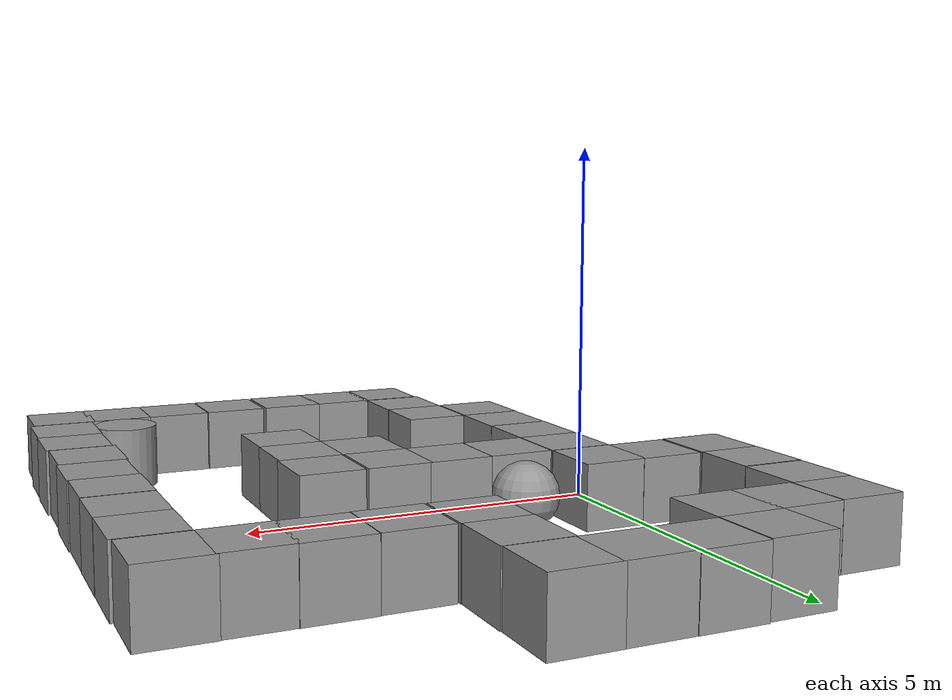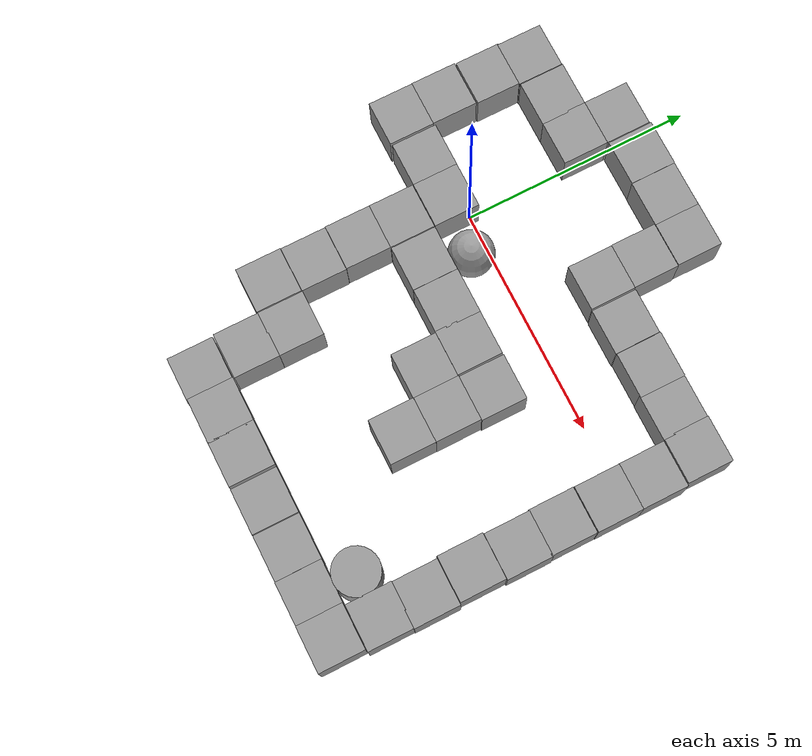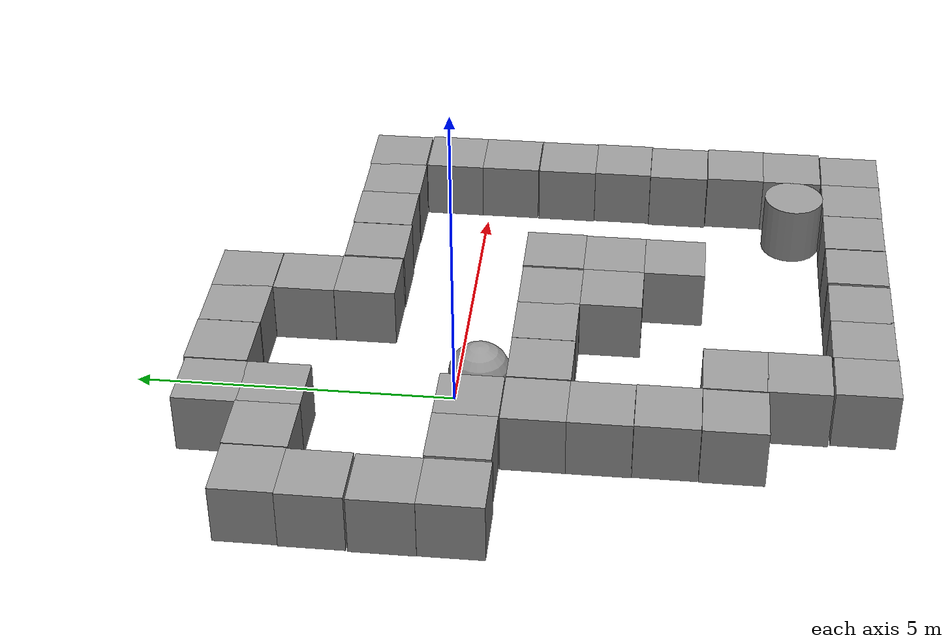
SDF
<?xml version='1.0'?>
<sdf version='1.7'>
  <model name='walls'>
    <model name='walls'>
      <link name='link'>
        <inertial>
          <mass>1</mass>
          <inertia>
            <ixx>0.166667</ixx>
            <ixy>0</ixy>
            <ixz>0</ixz>
            <iyy>0.166667</iyy>
            <iyz>0</iyz>
            <izz>0.166667</izz>
          </inertia>
          <pose>0 0 0 0 -0 0</pose>
        </inertial>
        <self_collide>0</self_collide>
        <enable_wind>0</enable_wind>
        <kinematic>0</kinematic>
        <pose>-0.512524 -0.284665 0 0 -0 0</pose>
        <visual name='visual'>
          <geometry>
            <box>
              <size>1 1 1</size>
            </box>
          </geometry>
          <material>
            <script>
              <name>Gazebo/Grey</name>
              <uri>file://media/materials/scripts/gazebo.material</uri>
            </script>
            <shader type='pixel'/>
          </material>
          <pose>0 0 0 0 -0 0</pose>
          <transparency>0</transparency>
          <cast_shadows>1</cast_shadows>
        </visual>
        <collision name='collision'>
          <laser_retro>0</laser_retro>
          <max_contacts>10</max_contacts>
          <pose>0 0 0 0 -0 0</pose>
          <geometry>
            <box>
              <size>1 1 1</size>
            </box>
          </geometry>
          <surface>
            <friction>
              <ode>
                <mu>1</mu>
                <mu2>1</mu2>
                <fdir1>0 0 0</fdir1>
                <slip1>0</slip1>
                <slip2>0</slip2>
              </ode>
              <torsional>
                <coefficient>1</coefficient>
                <patch_radius>0</patch_radius>
                <surface_radius>0</surface_radius>
                <use_patch_radius>1</use_patch_radius>
                <ode>
                  <slip>0</slip>
                </ode>
              </torsional>
            </friction>
            <bounce>
              <restitution_coefficient>0</restitution_coefficient>
              <threshold>1e+06</threshold>
            </bounce>
            <contact>
              <collide_without_contact>0</collide_without_contact>
              <collide_without_contact_bitmask>1</collide_without_contact_bitmask>
              <collide_bitmask>1</collide_bitmask>
              <ode>
                <soft_cfm>0</soft_cfm>
                <soft_erp>0.2</soft_erp>
                <kp>1e+13</kp>
                <kd>1</kd>
                <max_vel>0.01</max_vel>
                <min_depth>0</min_depth>
              </ode>
              <bullet>
                <split_impulse>1</split_impulse>
                <split_impulse_penetration_threshold>-0.01</split_impulse_penetration_threshold>
                <soft_cfm>0</soft_cfm>
                <soft_erp>0.2</soft_erp>
                <kp>1e+13</kp>
                <kd>1</kd>
              </bullet>
            </contact>
          </surface>
        </collision>
      </link>
      <link name='link_1'>
        <inertial>
          <mass>1</mass>
          <inertia>
            <ixx>0.166667</ixx>
            <ixy>0</ixy>
            <ixz>0</ixz>
            <iyy>0.166667</iyy>
            <iyz>0</iyz>
            <izz>0.166667</izz>
          </inertia>
        </inertial>
        <pose>-0.512524 -1.29814 0 0 -0 0</pose>
        <visual name='visual'>
          <pose>0 0 0 0 -0 0</pose>
          <geometry>
            <box>
              <size>1 1 1</size>
            </box>
          </geometry>
          <material>
            <lighting>1</lighting>
            <script>
              <uri>file://media/materials/scripts/gazebo.material</uri>
              <name>Gazebo/Grey</name>
            </script>
            <shader type='pixel'/>
          </material>
          <transparency>0</transparency>
          <cast_shadows>1</cast_shadows>
        </visual>
        <collision name='collision'>
          <laser_retro>0</laser_retro>
          <max_contacts>10</max_contacts>
          <pose>0 0 0 0 -0 0</pose>
          <geometry>
            <box>
              <size>1 1 1</size>
            </box>
          </geometry>
          <surface>
            <friction>
              <ode>
                <mu>1</mu>
                <mu2>1</mu2>
                <fdir1>0 0 0</fdir1>
                <slip1>0</slip1>
                <slip2>0</slip2>
              </ode>
              <torsional>
                <coefficient>1</coefficient>
                <patch_radius>0</patch_radius>
                <surface_radius>0</surface_radius>
                <use_patch_radius>1</use_patch_radius>
                <ode>
                  <slip>0</slip>
                </ode>
              </torsional>
            </friction>
            <bounce>
              <restitution_coefficient>0</restitution_coefficient>
              <threshold>1e+06</threshold>
            </bounce>
            <contact>
              <collide_without_contact>0</collide_without_contact>
              <collide_without_contact_bitmask>1</collide_without_contact_bitmask>
              <collide_bitmask>1</collide_bitmask>
              <ode>
                <soft_cfm>0</soft_cfm>
                <soft_erp>0.2</soft_erp>
                <kp>1e+13</kp>
                <kd>1</kd>
                <max_vel>0.01</max_vel>
                <min_depth>0</min_depth>
              </ode>
              <bullet>
                <split_impulse>1</split_impulse>
                <split_impulse_penetration_threshold>-0.01</split_impulse_penetration_threshold>
                <soft_cfm>0</soft_cfm>
                <soft_erp>0.2</soft_erp>
                <kp>1e+13</kp>
                <kd>1</kd>
              </bullet>
            </contact>
          </surface>
        </collision>
      </link>
      <link name='link_10'>
        <inertial>
          <mass>1</mass>
          <inertia>
            <ixx>0.166667</ixx>
            <ixy>0</ixy>
            <ixz>0</ixz>
            <iyy>0.166667</iyy>
            <iyz>0</iyz>
            <izz>0.166667</izz>
          </inertia>
        </inertial>
        <pose>2.49417 1.71182 0 0 -0 0</pose>
        <visual name='visual'>
          <pose>0 0 0 0 -0 0</pose>
          <geometry>
            <box>
              <size>1 1 1</size>
            </box>
          </geometry>
          <material>
            <lighting>1</lighting>
            <script>
              <uri>file://media/materials/scripts/gazebo.material</uri>
              <name>Gazebo/Grey</name>
            </script>
            <shader type='pixel'/>
          </material>
          <transparency>0</transparency>
          <cast_shadows>1</cast_shadows>
        </visual>
        <collision name='collision'>
          <laser_retro>0</laser_retro>
          <max_contacts>10</max_contacts>
          <pose>0 0 0 0 -0 0</pose>
          <geometry>
            <box>
              <size>1 1 1</size>
            </box>
          </geometry>
          <surface>
            <friction>
              <ode>
                <mu>1</mu>
                <mu2>1</mu2>
                <fdir1>0 0 0</fdir1>
                <slip1>0</slip1>
                <slip2>0</slip2>
              </ode>
              <torsional>
                <coefficient>1</coefficient>
                <patch_radius>0</patch_radius>
                <surface_radius>0</surface_radius>
                <use_patch_radius>1</use_patch_radius>
                <ode>
                  <slip>0</slip>
                </ode>
              </torsional>
            </friction>
            <bounce>
              <restitution_coefficient>0</restitution_coefficient>
              <threshold>1e+06</threshold>
            </bounce>
            <contact>
              <collide_without_contact>0</collide_without_contact>
              <collide_without_contact_bitmask>1</collide_without_contact_bitmask>
              <collide_bitmask>1</collide_bitmask>
              <ode>
                <soft_cfm>0</soft_cfm>
                <soft_erp>0.2</soft_erp>
                <kp>1e+13</kp>
                <kd>1</kd>
                <max_vel>0.01</max_vel>
                <min_depth>0</min_depth>
              </ode>
              <bullet>
                <split_impulse>1</split_impulse>
                <split_impulse_penetration_threshold>-0.01</split_impulse_penetration_threshold>
                <soft_cfm>0</soft_cfm>
                <soft_erp>0.2</soft_erp>
                <kp>1e+13</kp>
                <kd>1</kd>
              </bullet>
            </contact>
          </surface>
        </collision>
      </link>
      <link name='link_11'>
        <inertial>
          <mass>1</mass>
          <inertia>
            <ixx>0.166667</ixx>
            <ixy>0</ixy>
            <ixz>0</ixz>
            <iyy>0.166667</iyy>
            <iyz>0</iyz>
            <izz>0.166667</izz>
          </inertia>
        </inertial>
        <pose>2.4855 2.71047 0 0 -0 0</pose>
        <visual name='visual'>
          <pose>0 0 0 0 -0 0</pose>
          <geometry>
            <box>
              <size>1 1 1</size>
            </box>
          </geometry>
          <material>
            <lighting>1</lighting>
            <script>
              <uri>file://media/materials/scripts/gazebo.material</uri>
              <name>Gazebo/Grey</name>
            </script>
            <shader type='pixel'/>
          </material>
          <transparency>0</transparency>
          <cast_shadows>1</cast_shadows>
        </visual>
        <collision name='collision'>
          <laser_retro>0</laser_retro>
          <max_contacts>10</max_contacts>
          <pose>0 0 0 0 -0 0</pose>
          <geometry>
            <box>
              <size>1 1 1</size>
            </box>
          </geometry>
          <surface>
            <friction>
              <ode>
                <mu>1</mu>
                <mu2>1</mu2>
                <fdir1>0 0 0</fdir1>
                <slip1>0</slip1>
                <slip2>0</slip2>
              </ode>
              <torsional>
                <coefficient>1</coefficient>
                <patch_radius>0</patch_radius>
                <surface_radius>0</surface_radius>
                <use_patch_radius>1</use_patch_radius>
                <ode>
                  <slip>0</slip>
                </ode>
              </torsional>
            </friction>
            <bounce>
              <restitution_coefficient>0</restitution_coefficient>
              <threshold>1e+06</threshold>
            </bounce>
            <contact>
              <collide_without_contact>0</collide_without_contact>
              <collide_without_contact_bitmask>1</collide_without_contact_bitmask>
              <collide_bitmask>1</collide_bitmask>
              <ode>
                <soft_cfm>0</soft_cfm>
                <soft_erp>0.2</soft_erp>
                <kp>1e+13</kp>
                <kd>1</kd>
                <max_vel>0.01</max_vel>
                <min_depth>0</min_depth>
              </ode>
              <bullet>
                <split_impulse>1</split_impulse>
                <split_impulse_penetration_threshold>-0.01</split_impulse_penetration_threshold>
                <soft_cfm>0</soft_cfm>
                <soft_erp>0.2</soft_erp>
                <kp>1e+13</kp>
                <kd>1</kd>
              </bullet>
            </contact>
          </surface>
        </collision>
      </link>
      <link name='link_12'>
        <inertial>
          <mass>1</mass>
          <inertia>
            <ixx>0.166667</ixx>
            <ixy>0</ixy>
            <ixz>0</ixz>
            <iyy>0.166667</iyy>
            <iyz>0</iyz>
            <izz>0.166667</izz>
          </inertia>
        </inertial>
        <pose>3.52638 1.70047 0 0 -0 0</pose>
        <visual name='visual'>
          <pose>0 0 0 0 -0 0</pose>
          <geometry>
            <box>
              <size>1 1 1</size>
            </box>
          </geometry>
          <material>
            <lighting>1</lighting>
            <script>
              <uri>file://media/materials/scripts/gazebo.material</uri>
              <name>Gazebo/Grey</name>
            </script>
            <shader type='pixel'/>
          </material>
          <transparency>0</transparency>
          <cast_shadows>1</cast_shadows>
        </visual>
        <collision name='collision'>
          <laser_retro>0</laser_retro>
          <max_contacts>10</max_contacts>
          <pose>0 0 0 0 -0 0</pose>
          <geometry>
            <box>
              <size>1 1 1</size>
            </box>
          </geometry>
          <surface>
            <friction>
              <ode>
                <mu>1</mu>
                <mu2>1</mu2>
                <fdir1>0 0 0</fdir1>
                <slip1>0</slip1>
                <slip2>0</slip2>
              </ode>
              <torsional>
                <coefficient>1</coefficient>
                <patch_radius>0</patch_radius>
                <surface_radius>0</surface_radius>
                <use_patch_radius>1</use_patch_radius>
                <ode>
                  <slip>0</slip>
                </ode>
              </torsional>
            </friction>
            <bounce>
              <restitution_coefficient>0</restitution_coefficient>
              <threshold>1e+06</threshold>
            </bounce>
            <contact>
              <collide_without_contact>0</collide_without_contact>
              <collide_without_contact_bitmask>1</collide_without_contact_bitmask>
              <collide_bitmask>1</collide_bitmask>
              <ode>
                <soft_cfm>0</soft_cfm>
                <soft_erp>0.2</soft_erp>
                <kp>1e+13</kp>
                <kd>1</kd>
                <max_vel>0.01</max_vel>
                <min_depth>0</min_depth>
              </ode>
              <bullet>
                <split_impulse>1</split_impulse>
                <split_impulse_penetration_threshold>-0.01</split_impulse_penetration_threshold>
                <soft_cfm>0</soft_cfm>
                <soft_erp>0.2</soft_erp>
                <kp>1e+13</kp>
                <kd>1</kd>
              </bullet>
            </contact>
          </surface>
        </collision>
      </link>
      <link name='link_13'>
        <inertial>
          <mass>1</mass>
          <inertia>
            <ixx>0.166667</ixx>
            <ixy>0</ixy>
            <ixz>0</ixz>
            <iyy>0.166667</iyy>
            <iyz>0</iyz>
            <izz>0.166667</izz>
          </inertia>
        </inertial>
        <pose>2.47599 -1.2978 0 0 -0 0</pose>
        <visual name='visual'>
          <pose>0 0 0 0 -0 0</pose>
          <geometry>
            <box>
              <size>1 1 1</size>
            </box>
          </geometry>
          <material>
            <lighting>1</lighting>
            <script>
              <uri>file://media/materials/scripts/gazebo.material</uri>
              <name>Gazebo/Grey</name>
            </script>
            <shader type='pixel'/>
          </material>
          <transparency>0</transparency>
          <cast_shadows>1</cast_shadows>
        </visual>
        <collision name='collision'>
          <laser_retro>0</laser_retro>
          <max_contacts>10</max_contacts>
          <pose>0 0 0 0 -0 0</pose>
          <geometry>
            <box>
              <size>1 1 1</size>
            </box>
          </geometry>
          <surface>
            <friction>
              <ode>
                <mu>1</mu>
                <mu2>1</mu2>
                <fdir1>0 0 0</fdir1>
                <slip1>0</slip1>
                <slip2>0</slip2>
              </ode>
              <torsional>
                <coefficient>1</coefficient>
                <patch_radius>0</patch_radius>
                <surface_radius>0</surface_radius>
                <use_patch_radius>1</use_patch_radius>
                <ode>
                  <slip>0</slip>
                </ode>
              </torsional>
            </friction>
            <bounce>
              <restitution_coefficient>0</restitution_coefficient>
              <threshold>1e+06</threshold>
            </bounce>
            <contact>
              <collide_without_contact>0</collide_without_contact>
              <collide_without_contact_bitmask>1</collide_without_contact_bitmask>
              <collide_bitmask>1</collide_bitmask>
              <ode>
                <soft_cfm>0</soft_cfm>
                <soft_erp>0.2</soft_erp>
                <kp>1e+13</kp>
                <kd>1</kd>
                <max_vel>0.01</max_vel>
                <min_depth>0</min_depth>
              </ode>
              <bullet>
                <split_impulse>1</split_impulse>
                <split_impulse_penetration_threshold>-0.01</split_impulse_penetration_threshold>
                <soft_cfm>0</soft_cfm>
                <soft_erp>0.2</soft_erp>
                <kp>1e+13</kp>
                <kd>1</kd>
              </bullet>
            </contact>
          </surface>
        </collision>
      </link>
      <link name='link_14'>
        <inertial>
          <mass>1</mass>
          <inertia>
            <ixx>0.166667</ixx>
            <ixy>0</ixy>
            <ixz>0</ixz>
            <iyy>0.166667</iyy>
            <iyz>0</iyz>
            <izz>0.166667</izz>
          </inertia>
        </inertial>
        <pose>3.51464 -1.29178 0 0 -0 0</pose>
        <visual name='visual'>
          <pose>0 0 0 0 -0 0</pose>
          <geometry>
            <box>
              <size>1 1 1</size>
            </box>
          </geometry>
          <material>
            <lighting>1</lighting>
            <script>
              <uri>file://media/materials/scripts/gazebo.material</uri>
              <name>Gazebo/Grey</name>
            </script>
            <shader type='pixel'/>
          </material>
          <transparency>0</transparency>
          <cast_shadows>1</cast_shadows>
        </visual>
        <collision name='collision'>
          <laser_retro>0</laser_retro>
          <max_contacts>10</max_contacts>
          <pose>0 0 0 0 -0 0</pose>
          <geometry>
            <box>
              <size>1 1 1</size>
            </box>
          </geometry>
          <surface>
            <friction>
              <ode>
                <mu>1</mu>
                <mu2>1</mu2>
                <fdir1>0 0 0</fdir1>
                <slip1>0</slip1>
                <slip2>0</slip2>
              </ode>
              <torsional>
                <coefficient>1</coefficient>
                <patch_radius>0</patch_radius>
                <surface_radius>0</surface_radius>
                <use_patch_radius>1</use_patch_radius>
                <ode>
                  <slip>0</slip>
                </ode>
              </torsional>
            </friction>
            <bounce>
              <restitution_coefficient>0</restitution_coefficient>
              <threshold>1e+06</threshold>
            </bounce>
            <contact>
              <collide_without_contact>0</collide_without_contact>
              <collide_without_contact_bitmask>1</collide_without_contact_bitmask>
              <collide_bitmask>1</collide_bitmask>
              <ode>
                <soft_cfm>0</soft_cfm>
                <soft_erp>0.2</soft_erp>
                <kp>1e+13</kp>
                <kd>1</kd>
                <max_vel>0.01</max_vel>
                <min_depth>0</min_depth>
              </ode>
              <bullet>
                <split_impulse>1</split_impulse>
                <split_impulse_penetration_threshold>-0.01</split_impulse_penetration_threshold>
                <soft_cfm>0</soft_cfm>
                <soft_erp>0.2</soft_erp>
                <kp>1e+13</kp>
                <kd>1</kd>
              </bullet>
            </contact>
          </surface>
        </collision>
      </link>
      <link name='link_15'>
        <inertial>
          <mass>1</mass>
          <inertia>
            <ixx>0.166667</ixx>
            <ixy>0</ixy>
            <ixz>0</ixz>
            <iyy>0.166667</iyy>
            <iyz>0</iyz>
            <izz>0.166667</izz>
          </inertia>
        </inertial>
        <pose>2.49984 -2.29834 0 0 -0 0</pose>
        <visual name='visual'>
          <pose>0 0 0 0 -0 0</pose>
          <geometry>
            <box>
              <size>1 1 1</size>
            </box>
          </geometry>
          <material>
            <lighting>1</lighting>
            <script>
              <uri>file://media/materials/scripts/gazebo.material</uri>
              <name>Gazebo/Grey</name>
            </script>
            <shader type='pixel'/>
          </material>
          <transparency>0</transparency>
          <cast_shadows>1</cast_shadows>
        </visual>
        <collision name='collision'>
          <laser_retro>0</laser_retro>
          <max_contacts>10</max_contacts>
          <pose>0 0 0 0 -0 0</pose>
          <geometry>
            <box>
              <size>1 1 1</size>
            </box>
          </geometry>
          <surface>
            <friction>
              <ode>
                <mu>1</mu>
                <mu2>1</mu2>
                <fdir1>0 0 0</fdir1>
                <slip1>0</slip1>
                <slip2>0</slip2>
              </ode>
              <torsional>
                <coefficient>1</coefficient>
                <patch_radius>0</patch_radius>
                <surface_radius>0</surface_radius>
                <use_patch_radius>1</use_patch_radius>
                <ode>
                  <slip>0</slip>
                </ode>
              </torsional>
            </friction>
            <bounce>
              <restitution_coefficient>0</restitution_coefficient>
              <threshold>1e+06</threshold>
            </bounce>
            <contact>
              <collide_without_contact>0</collide_without_contact>
              <collide_without_contact_bitmask>1</collide_without_contact_bitmask>
              <collide_bitmask>1</collide_bitmask>
              <ode>
                <soft_cfm>0</soft_cfm>
                <soft_erp>0.2</soft_erp>
                <kp>1e+13</kp>
                <kd>1</kd>
                <max_vel>0.01</max_vel>
                <min_depth>0</min_depth>
              </ode>
              <bullet>
                <split_impulse>1</split_impulse>
                <split_impulse_penetration_threshold>-0.01</split_impulse_penetration_threshold>
                <soft_cfm>0</soft_cfm>
                <soft_erp>0.2</soft_erp>
                <kp>1e+13</kp>
                <kd>1</kd>
              </bullet>
            </contact>
          </surface>
        </collision>
      </link>
      <link name='link_16'>
        <inertial>
          <mass>1</mass>
          <inertia>
            <ixx>0.166667</ixx>
            <ixy>0</ixy>
            <ixz>0</ixz>
            <iyy>0.166667</iyy>
            <iyz>0</iyz>
            <izz>0.166667</izz>
          </inertia>
        </inertial>
        <pose>-0.501388 -3.299 0 0 -0 0</pose>
        <visual name='visual'>
          <pose>0 0 0 0 -0 0</pose>
          <geometry>
            <box>
              <size>1 1 1</size>
            </box>
          </geometry>
          <material>
            <lighting>1</lighting>
            <script>
              <uri>file://media/materials/scripts/gazebo.material</uri>
              <name>Gazebo/Grey</name>
            </script>
            <shader type='pixel'/>
          </material>
          <transparency>0</transparency>
          <cast_shadows>1</cast_shadows>
        </visual>
        <collision name='collision'>
          <laser_retro>0</laser_retro>
          <max_contacts>10</max_contacts>
          <pose>0 0 0 0 -0 0</pose>
          <geometry>
            <box>
              <size>1 1 1</size>
            </box>
          </geometry>
          <surface>
            <friction>
              <ode>
                <mu>1</mu>
                <mu2>1</mu2>
                <fdir1>0 0 0</fdir1>
                <slip1>0</slip1>
                <slip2>0</slip2>
              </ode>
              <torsional>
                <coefficient>1</coefficient>
                <patch_radius>0</patch_radius>
                <surface_radius>0</surface_radius>
                <use_patch_radius>1</use_patch_radius>
                <ode>
                  <slip>0</slip>
                </ode>
              </torsional>
            </friction>
            <bounce>
              <restitution_coefficient>0</restitution_coefficient>
              <threshold>1e+06</threshold>
            </bounce>
            <contact>
              <collide_without_contact>0</collide_without_contact>
              <collide_without_contact_bitmask>1</collide_without_contact_bitmask>
              <collide_bitmask>1</collide_bitmask>
              <ode>
                <soft_cfm>0</soft_cfm>
                <soft_erp>0.2</soft_erp>
                <kp>1e+13</kp>
                <kd>1</kd>
                <max_vel>0.01</max_vel>
                <min_depth>0</min_depth>
              </ode>
              <bullet>
                <split_impulse>1</split_impulse>
                <split_impulse_penetration_threshold>-0.01</split_impulse_penetration_threshold>
                <soft_cfm>0</soft_cfm>
                <soft_erp>0.2</soft_erp>
                <kp>1e+13</kp>
                <kd>1</kd>
              </bullet>
            </contact>
          </surface>
        </collision>
      </link>
      <link name='link_17'>
        <inertial>
          <mass>1</mass>
          <inertia>
            <ixx>0.166667</ixx>
            <ixy>0</ixy>
            <ixz>0</ixz>
            <iyy>0.166667</iyy>
            <iyz>0</iyz>
            <izz>0.166667</izz>
          </inertia>
        </inertial>
        <pose>-0.512524 -4.30435 0 0 -0 0</pose>
        <visual name='visual'>
          <pose>0 0 0 0 -0 0</pose>
          <geometry>
            <box>
              <size>1 1 1</size>
            </box>
          </geometry>
          <material>
            <lighting>1</lighting>
            <script>
              <uri>file://media/materials/scripts/gazebo.material</uri>
              <name>Gazebo/Grey</name>
            </script>
            <shader type='pixel'/>
          </material>
          <transparency>0</transparency>
          <cast_shadows>1</cast_shadows>
        </visual>
        <collision name='collision'>
          <laser_retro>0</laser_retro>
          <max_contacts>10</max_contacts>
          <pose>0 0 0 0 -0 0</pose>
          <geometry>
            <box>
              <size>1 1 1</size>
            </box>
          </geometry>
          <surface>
            <friction>
              <ode>
                <mu>1</mu>
                <mu2>1</mu2>
                <fdir1>0 0 0</fdir1>
                <slip1>0</slip1>
                <slip2>0</slip2>
              </ode>
              <torsional>
                <coefficient>1</coefficient>
                <patch_radius>0</patch_radius>
                <surface_radius>0</surface_radius>
                <use_patch_radius>1</use_patch_radius>
                <ode>
                  <slip>0</slip>
                </ode>
              </torsional>
            </friction>
            <bounce>
              <restitution_coefficient>0</restitution_coefficient>
              <threshold>1e+06</threshold>
            </bounce>
            <contact>
              <collide_without_contact>0</collide_without_contact>
              <collide_without_contact_bitmask>1</collide_without_contact_bitmask>
              <collide_bitmask>1</collide_bitmask>
              <ode>
                <soft_cfm>0</soft_cfm>
                <soft_erp>0.2</soft_erp>
                <kp>1e+13</kp>
                <kd>1</kd>
                <max_vel>0.01</max_vel>
                <min_depth>0</min_depth>
              </ode>
              <bullet>
                <split_impulse>1</split_impulse>
                <split_impulse_penetration_threshold>-0.01</split_impulse_penetration_threshold>
                <soft_cfm>0</soft_cfm>
                <soft_erp>0.2</soft_erp>
                <kp>1e+13</kp>
                <kd>1</kd>
              </bullet>
            </contact>
          </surface>
        </collision>
      </link>
      <link name='link_18'>
        <inertial>
          <mass>1</mass>
          <inertia>
            <ixx>0.166667</ixx>
            <ixy>0</ixy>
            <ixz>0</ixz>
            <iyy>0.166667</iyy>
            <iyz>0</iyz>
            <izz>0.166667</izz>
          </inertia>
        </inertial>
        <pose>0.508816 -4.29524 0 0 -0 0</pose>
        <visual name='visual'>
          <pose>0 0 0 0 -0 0</pose>
          <geometry>
            <box>
              <size>1 1 1</size>
            </box>
          </geometry>
          <material>
            <lighting>1</lighting>
            <script>
              <uri>file://media/materials/scripts/gazebo.material</uri>
              <name>Gazebo/Grey</name>
            </script>
            <shader type='pixel'/>
          </material>
          <transparency>0</transparency>
          <cast_shadows>1</cast_shadows>
        </visual>
        <collision name='collision'>
          <laser_retro>0</laser_retro>
          <max_contacts>10</max_contacts>
          <pose>0 0 0 0 -0 0</pose>
          <geometry>
            <box>
              <size>1 1 1</size>
            </box>
          </geometry>
          <surface>
            <friction>
              <ode>
                <mu>1</mu>
                <mu2>1</mu2>
                <fdir1>0 0 0</fdir1>
                <slip1>0</slip1>
                <slip2>0</slip2>
              </ode>
              <torsional>
                <coefficient>1</coefficient>
                <patch_radius>0</patch_radius>
                <surface_radius>0</surface_radius>
                <use_patch_radius>1</use_patch_radius>
                <ode>
                  <slip>0</slip>
                </ode>
              </torsional>
            </friction>
            <bounce>
              <restitution_coefficient>0</restitution_coefficient>
              <threshold>1e+06</threshold>
            </bounce>
            <contact>
              <collide_without_contact>0</collide_without_contact>
              <collide_without_contact_bitmask>1</collide_without_contact_bitmask>
              <collide_bitmask>1</collide_bitmask>
              <ode>
                <soft_cfm>0</soft_cfm>
                <soft_erp>0.2</soft_erp>
                <kp>1e+13</kp>
                <kd>1</kd>
                <max_vel>0.01</max_vel>
                <min_depth>0</min_depth>
              </ode>
              <bullet>
                <split_impulse>1</split_impulse>
                <split_impulse_penetration_threshold>-0.01</split_impulse_penetration_threshold>
                <soft_cfm>0</soft_cfm>
                <soft_erp>0.2</soft_erp>
                <kp>1e+13</kp>
                <kd>1</kd>
              </bullet>
            </contact>
          </surface>
        </collision>
      </link>
      <link name='link_19'>
        <inertial>
          <mass>1</mass>
          <inertia>
            <ixx>0.166667</ixx>
            <ixy>0</ixy>
            <ixz>0</ixz>
            <iyy>0.166667</iyy>
            <iyz>0</iyz>
            <izz>0.166667</izz>
          </inertia>
        </inertial>
        <pose>3.4913 -2.29195 0 0 -0 0</pose>
        <visual name='visual'>
          <pose>0 0 0 0 -0 0</pose>
          <geometry>
            <box>
              <size>1 1 1</size>
            </box>
          </geometry>
          <material>
            <lighting>1</lighting>
            <script>
              <uri>file://media/materials/scripts/gazebo.material</uri>
              <name>Gazebo/Grey</name>
            </script>
            <shader type='pixel'/>
          </material>
          <transparency>0</transparency>
          <cast_shadows>1</cast_shadows>
        </visual>
        <collision name='collision'>
          <laser_retro>0</laser_retro>
          <max_contacts>10</max_contacts>
          <pose>0 0 0 0 -0 0</pose>
          <geometry>
            <box>
              <size>1 1 1</size>
            </box>
          </geometry>
          <surface>
            <friction>
              <ode>
                <mu>1</mu>
                <mu2>1</mu2>
                <fdir1>0 0 0</fdir1>
                <slip1>0</slip1>
                <slip2>0</slip2>
              </ode>
              <torsional>
                <coefficient>1</coefficient>
                <patch_radius>0</patch_radius>
                <surface_radius>0</surface_radius>
                <use_patch_radius>1</use_patch_radius>
                <ode>
                  <slip>0</slip>
                </ode>
              </torsional>
            </friction>
            <bounce>
              <restitution_coefficient>0</restitution_coefficient>
              <threshold>1e+06</threshold>
            </bounce>
            <contact>
              <collide_without_contact>0</collide_without_contact>
              <collide_without_contact_bitmask>1</collide_without_contact_bitmask>
              <collide_bitmask>1</collide_bitmask>
              <ode>
                <soft_cfm>0</soft_cfm>
                <soft_erp>0.2</soft_erp>
                <kp>1e+13</kp>
                <kd>1</kd>
                <max_vel>0.01</max_vel>
                <min_depth>0</min_depth>
              </ode>
              <bullet>
                <split_impulse>1</split_impulse>
                <split_impulse_penetration_threshold>-0.01</split_impulse_penetration_threshold>
                <soft_cfm>0</soft_cfm>
                <soft_erp>0.2</soft_erp>
                <kp>1e+13</kp>
                <kd>1</kd>
              </bullet>
            </contact>
          </surface>
        </collision>
      </link>
      <link name='link_2'>
        <inertial>
          <mass>1</mass>
          <inertia>
            <ixx>0.166667</ixx>
            <ixy>0</ixy>
            <ixz>0</ixz>
            <iyy>0.166667</iyy>
            <iyz>0</iyz>
            <izz>0.166667</izz>
          </inertia>
        </inertial>
        <pose>-0.512524 -2.29392 0 0 -0 0</pose>
        <visual name='visual'>
          <pose>0 0 0 0 -0 0</pose>
          <geometry>
            <box>
              <size>1 1 1</size>
            </box>
          </geometry>
          <material>
            <lighting>1</lighting>
            <script>
              <uri>file://media/materials/scripts/gazebo.material</uri>
              <name>Gazebo/Grey</name>
            </script>
            <shader type='pixel'/>
          </material>
          <transparency>0</transparency>
          <cast_shadows>1</cast_shadows>
        </visual>
        <collision name='collision'>
          <laser_retro>0</laser_retro>
          <max_contacts>10</max_contacts>
          <pose>0 0 0 0 -0 0</pose>
          <geometry>
            <box>
              <size>1 1 1</size>
            </box>
          </geometry>
          <surface>
            <friction>
              <ode>
                <mu>1</mu>
                <mu2>1</mu2>
                <fdir1>0 0 0</fdir1>
                <slip1>0</slip1>
                <slip2>0</slip2>
              </ode>
              <torsional>
                <coefficient>1</coefficient>
                <patch_radius>0</patch_radius>
                <surface_radius>0</surface_radius>
                <use_patch_radius>1</use_patch_radius>
                <ode>
                  <slip>0</slip>
                </ode>
              </torsional>
            </friction>
            <bounce>
              <restitution_coefficient>0</restitution_coefficient>
              <threshold>1e+06</threshold>
            </bounce>
            <contact>
              <collide_without_contact>0</collide_without_contact>
              <collide_without_contact_bitmask>1</collide_without_contact_bitmask>
              <collide_bitmask>1</collide_bitmask>
              <ode>
                <soft_cfm>0</soft_cfm>
                <soft_erp>0.2</soft_erp>
                <kp>1e+13</kp>
                <kd>1</kd>
                <max_vel>0.01</max_vel>
                <min_depth>0</min_depth>
              </ode>
              <bullet>
                <split_impulse>1</split_impulse>
                <split_impulse_penetration_threshold>-0.01</split_impulse_penetration_threshold>
                <soft_cfm>0</soft_cfm>
                <soft_erp>0.2</soft_erp>
                <kp>1e+13</kp>
                <kd>1</kd>
              </bullet>
            </contact>
          </surface>
        </collision>
      </link>
      <link name='link_20'>
        <inertial>
          <mass>1</mass>
          <inertia>
            <ixx>0.166667</ixx>
            <ixy>0</ixy>
            <ixz>0</ixz>
            <iyy>0.166667</iyy>
            <iyz>0</iyz>
            <izz>0.166667</izz>
          </inertia>
        </inertial>
        <pose>3.48594 -3.29211 0 0 -0 0</pose>
        <visual name='visual'>
          <pose>0 0 0 0 -0 0</pose>
          <geometry>
            <box>
              <size>1 1 1</size>
            </box>
          </geometry>
          <material>
            <lighting>1</lighting>
            <script>
              <uri>file://media/materials/scripts/gazebo.material</uri>
              <name>Gazebo/Grey</name>
            </script>
            <shader type='pixel'/>
          </material>
          <transparency>0</transparency>
          <cast_shadows>1</cast_shadows>
        </visual>
        <collision name='collision'>
          <laser_retro>0</laser_retro>
          <max_contacts>10</max_contacts>
          <pose>0 0 0 0 -0 0</pose>
          <geometry>
            <box>
              <size>1 1 1</size>
            </box>
          </geometry>
          <surface>
            <friction>
              <ode>
                <mu>1</mu>
                <mu2>1</mu2>
                <fdir1>0 0 0</fdir1>
                <slip1>0</slip1>
                <slip2>0</slip2>
              </ode>
              <torsional>
                <coefficient>1</coefficient>
                <patch_radius>0</patch_radius>
                <surface_radius>0</surface_radius>
                <use_patch_radius>1</use_patch_radius>
                <ode>
                  <slip>0</slip>
                </ode>
              </torsional>
            </friction>
            <bounce>
              <restitution_coefficient>0</restitution_coefficient>
              <threshold>1e+06</threshold>
            </bounce>
            <contact>
              <collide_without_contact>0</collide_without_contact>
              <collide_without_contact_bitmask>1</collide_without_contact_bitmask>
              <collide_bitmask>1</collide_bitmask>
              <ode>
                <soft_cfm>0</soft_cfm>
                <soft_erp>0.2</soft_erp>
                <kp>1e+13</kp>
                <kd>1</kd>
                <max_vel>0.01</max_vel>
                <min_depth>0</min_depth>
              </ode>
              <bullet>
                <split_impulse>1</split_impulse>
                <split_impulse_penetration_threshold>-0.01</split_impulse_penetration_threshold>
                <soft_cfm>0</soft_cfm>
                <soft_erp>0.2</soft_erp>
                <kp>1e+13</kp>
                <kd>1</kd>
              </bullet>
            </contact>
          </surface>
        </collision>
      </link>
      <link name='link_21'>
        <inertial>
          <mass>1</mass>
          <inertia>
            <ixx>0.166667</ixx>
            <ixy>0</ixy>
            <ixz>0</ixz>
            <iyy>0.166667</iyy>
            <iyz>0</iyz>
            <izz>0.166667</izz>
          </inertia>
        </inertial>
        <pose>-1.47979 -0.28195 0 0 -0 0</pose>
        <visual name='visual'>
          <pose>0 0 0 0 -0 0</pose>
          <geometry>
            <box>
              <size>1 1 1</size>
            </box>
          </geometry>
          <material>
            <lighting>1</lighting>
            <script>
              <uri>file://media/materials/scripts/gazebo.material</uri>
              <name>Gazebo/Grey</name>
            </script>
            <shader type='pixel'/>
          </material>
          <transparency>0</transparency>
          <cast_shadows>1</cast_shadows>
        </visual>
        <collision name='collision'>
          <laser_retro>0</laser_retro>
          <max_contacts>10</max_contacts>
          <pose>0 0 0 0 -0 0</pose>
          <geometry>
            <box>
              <size>1 1 1</size>
            </box>
          </geometry>
          <surface>
            <friction>
              <ode>
                <mu>1</mu>
                <mu2>1</mu2>
                <fdir1>0 0 0</fdir1>
                <slip1>0</slip1>
                <slip2>0</slip2>
              </ode>
              <torsional>
                <coefficient>1</coefficient>
                <patch_radius>0</patch_radius>
                <surface_radius>0</surface_radius>
                <use_patch_radius>1</use_patch_radius>
                <ode>
                  <slip>0</slip>
                </ode>
              </torsional>
            </friction>
            <bounce>
              <restitution_coefficient>0</restitution_coefficient>
              <threshold>1e+06</threshold>
            </bounce>
            <contact>
              <collide_without_contact>0</collide_without_contact>
              <collide_without_contact_bitmask>1</collide_without_contact_bitmask>
              <collide_bitmask>1</collide_bitmask>
              <ode>
                <soft_cfm>0</soft_cfm>
                <soft_erp>0.2</soft_erp>
                <kp>1e+13</kp>
                <kd>1</kd>
                <max_vel>0.01</max_vel>
                <min_depth>0</min_depth>
              </ode>
              <bullet>
                <split_impulse>1</split_impulse>
                <split_impulse_penetration_threshold>-0.01</split_impulse_penetration_threshold>
                <soft_cfm>0</soft_cfm>
                <soft_erp>0.2</soft_erp>
                <kp>1e+13</kp>
                <kd>1</kd>
              </bullet>
            </contact>
          </surface>
        </collision>
      </link>
      <link name='link_22'>
        <inertial>
          <mass>1</mass>
          <inertia>
            <ixx>0.166667</ixx>
            <ixy>0</ixy>
            <ixz>0</ixz>
            <iyy>0.166667</iyy>
            <iyz>0</iyz>
            <izz>0.166667</izz>
          </inertia>
        </inertial>
        <pose>-1.47979 2.7064 0 0 -0 0</pose>
        <visual name='visual'>
          <pose>0 0 0 0 -0 0</pose>
          <geometry>
            <box>
              <size>1 1 1</size>
            </box>
          </geometry>
          <material>
            <lighting>1</lighting>
            <script>
              <uri>file://media/materials/scripts/gazebo.material</uri>
              <name>Gazebo/Grey</name>
            </script>
            <shader type='pixel'/>
          </material>
          <transparency>0</transparency>
          <cast_shadows>1</cast_shadows>
        </visual>
        <collision name='collision'>
          <laser_retro>0</laser_retro>
          <max_contacts>10</max_contacts>
          <pose>0 0 0 0 -0 0</pose>
          <geometry>
            <box>
              <size>1 1 1</size>
            </box>
          </geometry>
          <surface>
            <friction>
              <ode>
                <mu>1</mu>
                <mu2>1</mu2>
                <fdir1>0 0 0</fdir1>
                <slip1>0</slip1>
                <slip2>0</slip2>
              </ode>
              <torsional>
                <coefficient>1</coefficient>
                <patch_radius>0</patch_radius>
                <surface_radius>0</surface_radius>
                <use_patch_radius>1</use_patch_radius>
                <ode>
                  <slip>0</slip>
                </ode>
              </torsional>
            </friction>
            <bounce>
              <restitution_coefficient>0</restitution_coefficient>
              <threshold>1e+06</threshold>
            </bounce>
            <contact>
              <collide_without_contact>0</collide_without_contact>
              <collide_without_contact_bitmask>1</collide_without_contact_bitmask>
              <collide_bitmask>1</collide_bitmask>
              <ode>
                <soft_cfm>0</soft_cfm>
                <soft_erp>0.2</soft_erp>
                <kp>1e+13</kp>
                <kd>1</kd>
                <max_vel>0.01</max_vel>
                <min_depth>0</min_depth>
              </ode>
              <bullet>
                <split_impulse>1</split_impulse>
                <split_impulse_penetration_threshold>-0.01</split_impulse_penetration_threshold>
                <soft_cfm>0</soft_cfm>
                <soft_erp>0.2</soft_erp>
                <kp>1e+13</kp>
                <kd>1</kd>
              </bullet>
            </contact>
          </surface>
        </collision>
      </link>
      <link name='link_23'>
        <inertial>
          <mass>1</mass>
          <inertia>
            <ixx>0.166667</ixx>
            <ixy>0</ixy>
            <ixz>0</ixz>
            <iyy>0.166667</iyy>
            <iyz>0</iyz>
            <izz>0.166667</izz>
          </inertia>
        </inertial>
        <pose>-2.5242 -0.30388 0 0 -0 0</pose>
        <visual name='visual'>
          <pose>0 0 0 0 -0 0</pose>
          <geometry>
            <box>
              <size>1 1 1</size>
            </box>
          </geometry>
          <material>
            <lighting>1</lighting>
            <script>
              <uri>file://media/materials/scripts/gazebo.material</uri>
              <name>Gazebo/Grey</name>
            </script>
            <shader type='pixel'/>
          </material>
          <transparency>0</transparency>
          <cast_shadows>1</cast_shadows>
        </visual>
        <collision name='collision'>
          <laser_retro>0</laser_retro>
          <max_contacts>10</max_contacts>
          <pose>0 0 0 0 -0 0</pose>
          <geometry>
            <box>
              <size>1 1 1</size>
            </box>
          </geometry>
          <surface>
            <friction>
              <ode>
                <mu>1</mu>
                <mu2>1</mu2>
                <fdir1>0 0 0</fdir1>
                <slip1>0</slip1>
                <slip2>0</slip2>
              </ode>
              <torsional>
                <coefficient>1</coefficient>
                <patch_radius>0</patch_radius>
                <surface_radius>0</surface_radius>
                <use_patch_radius>1</use_patch_radius>
                <ode>
                  <slip>0</slip>
                </ode>
              </torsional>
            </friction>
            <bounce>
              <restitution_coefficient>0</restitution_coefficient>
              <threshold>1e+06</threshold>
            </bounce>
            <contact>
              <collide_without_contact>0</collide_without_contact>
              <collide_without_contact_bitmask>1</collide_without_contact_bitmask>
              <collide_bitmask>1</collide_bitmask>
              <ode>
                <soft_cfm>0</soft_cfm>
                <soft_erp>0.2</soft_erp>
                <kp>1e+13</kp>
                <kd>1</kd>
                <max_vel>0.01</max_vel>
                <min_depth>0</min_depth>
              </ode>
              <bullet>
                <split_impulse>1</split_impulse>
                <split_impulse_penetration_threshold>-0.01</split_impulse_penetration_threshold>
                <soft_cfm>0</soft_cfm>
                <soft_erp>0.2</soft_erp>
                <kp>1e+13</kp>
                <kd>1</kd>
              </bullet>
            </contact>
          </surface>
        </collision>
      </link>
      <link name='link_24'>
        <inertial>
          <mass>1</mass>
          <inertia>
            <ixx>0.166667</ixx>
            <ixy>0</ixy>
            <ixz>0</ixz>
            <iyy>0.166667</iyy>
            <iyz>0</iyz>
            <izz>0.166667</izz>
          </inertia>
        </inertial>
        <pose>-2.52977 0.694085 0 0 -0 0</pose>
        <visual name='visual'>
          <pose>0 0 0 0 -0 0</pose>
          <geometry>
            <box>
              <size>1 1 1</size>
            </box>
          </geometry>
          <material>
            <lighting>1</lighting>
            <script>
              <uri>file://media/materials/scripts/gazebo.material</uri>
              <name>Gazebo/Grey</name>
            </script>
            <shader type='pixel'/>
          </material>
          <transparency>0</transparency>
          <cast_shadows>1</cast_shadows>
        </visual>
        <collision name='collision'>
          <laser_retro>0</laser_retro>
          <max_contacts>10</max_contacts>
          <pose>0 0 0 0 -0 0</pose>
          <geometry>
            <box>
              <size>1 1 1</size>
            </box>
          </geometry>
          <surface>
            <friction>
              <ode>
                <mu>1</mu>
                <mu2>1</mu2>
                <fdir1>0 0 0</fdir1>
                <slip1>0</slip1>
                <slip2>0</slip2>
              </ode>
              <torsional>
                <coefficient>1</coefficient>
                <patch_radius>0</patch_radius>
                <surface_radius>0</surface_radius>
                <use_patch_radius>1</use_patch_radius>
                <ode>
                  <slip>0</slip>
                </ode>
              </torsional>
            </friction>
            <bounce>
              <restitution_coefficient>0</restitution_coefficient>
              <threshold>1e+06</threshold>
            </bounce>
            <contact>
              <collide_without_contact>0</collide_without_contact>
              <collide_without_contact_bitmask>1</collide_without_contact_bitmask>
              <collide_bitmask>1</collide_bitmask>
              <ode>
                <soft_cfm>0</soft_cfm>
                <soft_erp>0.2</soft_erp>
                <kp>1e+13</kp>
                <kd>1</kd>
                <max_vel>0.01</max_vel>
                <min_depth>0</min_depth>
              </ode>
              <bullet>
                <split_impulse>1</split_impulse>
                <split_impulse_penetration_threshold>-0.01</split_impulse_penetration_threshold>
                <soft_cfm>0</soft_cfm>
                <soft_erp>0.2</soft_erp>
                <kp>1e+13</kp>
                <kd>1</kd>
              </bullet>
            </contact>
          </surface>
        </collision>
      </link>
      <link name='link_25'>
        <inertial>
          <mass>1</mass>
          <inertia>
            <ixx>0.166667</ixx>
            <ixy>0</ixy>
            <ixz>0</ixz>
            <iyy>0.166667</iyy>
            <iyz>0</iyz>
            <izz>0.166667</izz>
          </inertia>
        </inertial>
        <pose>-2.51297 1.72301 0 0 -0 0</pose>
        <visual name='visual'>
          <pose>0 0 0 0 -0 0</pose>
          <geometry>
            <box>
              <size>1 1 1</size>
            </box>
          </geometry>
          <material>
            <lighting>1</lighting>
            <script>
              <uri>file://media/materials/scripts/gazebo.material</uri>
              <name>Gazebo/Grey</name>
            </script>
            <shader type='pixel'/>
          </material>
          <transparency>0</transparency>
          <cast_shadows>1</cast_shadows>
        </visual>
        <collision name='collision'>
          <laser_retro>0</laser_retro>
          <max_contacts>10</max_contacts>
          <pose>0 0 0 0 -0 0</pose>
          <geometry>
            <box>
              <size>1 1 1</size>
            </box>
          </geometry>
          <surface>
            <friction>
              <ode>
                <mu>1</mu>
                <mu2>1</mu2>
                <fdir1>0 0 0</fdir1>
                <slip1>0</slip1>
                <slip2>0</slip2>
              </ode>
              <torsional>
                <coefficient>1</coefficient>
                <patch_radius>0</patch_radius>
                <surface_radius>0</surface_radius>
                <use_patch_radius>1</use_patch_radius>
                <ode>
                  <slip>0</slip>
                </ode>
              </torsional>
            </friction>
            <bounce>
              <restitution_coefficient>0</restitution_coefficient>
              <threshold>1e+06</threshold>
            </bounce>
            <contact>
              <collide_without_contact>0</collide_without_contact>
              <collide_without_contact_bitmask>1</collide_without_contact_bitmask>
              <collide_bitmask>1</collide_bitmask>
              <ode>
                <soft_cfm>0</soft_cfm>
                <soft_erp>0.2</soft_erp>
                <kp>1e+13</kp>
                <kd>1</kd>
                <max_vel>0.01</max_vel>
                <min_depth>0</min_depth>
              </ode>
              <bullet>
                <split_impulse>1</split_impulse>
                <split_impulse_penetration_threshold>-0.01</split_impulse_penetration_threshold>
                <soft_cfm>0</soft_cfm>
                <soft_erp>0.2</soft_erp>
                <kp>1e+13</kp>
                <kd>1</kd>
              </bullet>
            </contact>
          </surface>
        </collision>
      </link>
      <link name='link_26'>
        <inertial>
          <mass>1</mass>
          <inertia>
            <ixx>0.166667</ixx>
            <ixy>0</ixy>
            <ixz>0</ixz>
            <iyy>0.166667</iyy>
            <iyz>0</iyz>
            <izz>0.166667</izz>
          </inertia>
        </inertial>
        <pose>-2.49446 2.69308 0 0 -0 0</pose>
        <visual name='visual'>
          <pose>0 0 0 0 -0 0</pose>
          <geometry>
            <box>
              <size>1 1 1</size>
            </box>
          </geometry>
          <material>
            <lighting>1</lighting>
            <script>
              <uri>file://media/materials/scripts/gazebo.material</uri>
              <name>Gazebo/Grey</name>
            </script>
            <shader type='pixel'/>
          </material>
          <transparency>0</transparency>
          <cast_shadows>1</cast_shadows>
        </visual>
        <collision name='collision'>
          <laser_retro>0</laser_retro>
          <max_contacts>10</max_contacts>
          <pose>0 0 0 0 -0 0</pose>
          <geometry>
            <box>
              <size>1 1 1</size>
            </box>
          </geometry>
          <surface>
            <friction>
              <ode>
                <mu>1</mu>
                <mu2>1</mu2>
                <fdir1>0 0 0</fdir1>
                <slip1>0</slip1>
                <slip2>0</slip2>
              </ode>
              <torsional>
                <coefficient>1</coefficient>
                <patch_radius>0</patch_radius>
                <surface_radius>0</surface_radius>
                <use_patch_radius>1</use_patch_radius>
                <ode>
                  <slip>0</slip>
                </ode>
              </torsional>
            </friction>
            <bounce>
              <restitution_coefficient>0</restitution_coefficient>
              <threshold>1e+06</threshold>
            </bounce>
            <contact>
              <collide_without_contact>0</collide_without_contact>
              <collide_without_contact_bitmask>1</collide_without_contact_bitmask>
              <collide_bitmask>1</collide_bitmask>
              <ode>
                <soft_cfm>0</soft_cfm>
                <soft_erp>0.2</soft_erp>
                <kp>1e+13</kp>
                <kd>1</kd>
                <max_vel>0.01</max_vel>
                <min_depth>0</min_depth>
              </ode>
              <bullet>
                <split_impulse>1</split_impulse>
                <split_impulse_penetration_threshold>-0.01</split_impulse_penetration_threshold>
                <soft_cfm>0</soft_cfm>
                <soft_erp>0.2</soft_erp>
                <kp>1e+13</kp>
                <kd>1</kd>
              </bullet>
            </contact>
          </surface>
        </collision>
      </link>
      <link name='link_27'>
        <inertial>
          <mass>1</mass>
          <inertia>
            <ixx>0.166667</ixx>
            <ixy>0</ixy>
            <ixz>0</ixz>
            <iyy>0.166667</iyy>
            <iyz>0</iyz>
            <izz>0.166667</izz>
          </inertia>
        </inertial>
        <pose>4.53296 1.71543 0 0 -0 0</pose>
        <visual name='visual'>
          <pose>0 0 0 0 -0 0</pose>
          <geometry>
            <box>
              <size>1 1 1</size>
            </box>
          </geometry>
          <material>
            <lighting>1</lighting>
            <script>
              <uri>file://media/materials/scripts/gazebo.material</uri>
              <name>Gazebo/Grey</name>
            </script>
            <shader type='pixel'/>
          </material>
          <transparency>0</transparency>
          <cast_shadows>1</cast_shadows>
        </visual>
        <collision name='collision'>
          <laser_retro>0</laser_retro>
          <max_contacts>10</max_contacts>
          <pose>0 0 0 0 -0 0</pose>
          <geometry>
            <box>
              <size>1 1 1</size>
            </box>
          </geometry>
          <surface>
            <friction>
              <ode>
                <mu>1</mu>
                <mu2>1</mu2>
                <fdir1>0 0 0</fdir1>
                <slip1>0</slip1>
                <slip2>0</slip2>
              </ode>
              <torsional>
                <coefficient>1</coefficient>
                <patch_radius>0</patch_radius>
                <surface_radius>0</surface_radius>
                <use_patch_radius>1</use_patch_radius>
                <ode>
                  <slip>0</slip>
                </ode>
              </torsional>
            </friction>
            <bounce>
              <restitution_coefficient>0</restitution_coefficient>
              <threshold>1e+06</threshold>
            </bounce>
            <contact>
              <collide_without_contact>0</collide_without_contact>
              <collide_without_contact_bitmask>1</collide_without_contact_bitmask>
              <collide_bitmask>1</collide_bitmask>
              <ode>
                <soft_cfm>0</soft_cfm>
                <soft_erp>0.2</soft_erp>
                <kp>1e+13</kp>
                <kd>1</kd>
                <max_vel>0.01</max_vel>
                <min_depth>0</min_depth>
              </ode>
              <bullet>
                <split_impulse>1</split_impulse>
                <split_impulse_penetration_threshold>-0.01</split_impulse_penetration_threshold>
                <soft_cfm>0</soft_cfm>
                <soft_erp>0.2</soft_erp>
                <kp>1e+13</kp>
                <kd>1</kd>
              </bullet>
            </contact>
          </surface>
        </collision>
      </link>
      <link name='link_28'>
        <inertial>
          <mass>1</mass>
          <inertia>
            <ixx>0.166667</ixx>
            <ixy>0</ixy>
            <ixz>0</ixz>
            <iyy>0.166667</iyy>
            <iyz>0</iyz>
            <izz>0.166667</izz>
          </inertia>
        </inertial>
        <pose>5.49069 1.70627 0 0 -0 0</pose>
        <visual name='visual'>
          <pose>0 0 0 0 -0 0</pose>
          <geometry>
            <box>
              <size>1 1 1</size>
            </box>
          </geometry>
          <material>
            <lighting>1</lighting>
            <script>
              <uri>file://media/materials/scripts/gazebo.material</uri>
              <name>Gazebo/Grey</name>
            </script>
            <shader type='pixel'/>
          </material>
          <transparency>0</transparency>
          <cast_shadows>1</cast_shadows>
        </visual>
        <collision name='collision'>
          <laser_retro>0</laser_retro>
          <max_contacts>10</max_contacts>
          <pose>0 0 0 0 -0 0</pose>
          <geometry>
            <box>
              <size>1 1 1</size>
            </box>
          </geometry>
          <surface>
            <friction>
              <ode>
                <mu>1</mu>
                <mu2>1</mu2>
                <fdir1>0 0 0</fdir1>
                <slip1>0</slip1>
                <slip2>0</slip2>
              </ode>
              <torsional>
                <coefficient>1</coefficient>
                <patch_radius>0</patch_radius>
                <surface_radius>0</surface_radius>
                <use_patch_radius>1</use_patch_radius>
                <ode>
                  <slip>0</slip>
                </ode>
              </torsional>
            </friction>
            <bounce>
              <restitution_coefficient>0</restitution_coefficient>
              <threshold>1e+06</threshold>
            </bounce>
            <contact>
              <collide_without_contact>0</collide_without_contact>
              <collide_without_contact_bitmask>1</collide_without_contact_bitmask>
              <collide_bitmask>1</collide_bitmask>
              <ode>
                <soft_cfm>0</soft_cfm>
                <soft_erp>0.2</soft_erp>
                <kp>1e+13</kp>
                <kd>1</kd>
                <max_vel>0.01</max_vel>
                <min_depth>0</min_depth>
              </ode>
              <bullet>
                <split_impulse>1</split_impulse>
                <split_impulse_penetration_threshold>-0.01</split_impulse_penetration_threshold>
                <soft_cfm>0</soft_cfm>
                <soft_erp>0.2</soft_erp>
                <kp>1e+13</kp>
                <kd>1</kd>
              </bullet>
            </contact>
          </surface>
        </collision>
      </link>
      <link name='link_29'>
        <inertial>
          <mass>1</mass>
          <inertia>
            <ixx>0.166667</ixx>
            <ixy>0</ixy>
            <ixz>0</ixz>
            <iyy>0.166667</iyy>
            <iyz>0</iyz>
            <izz>0.166667</izz>
          </inertia>
        </inertial>
        <pose>6.45702 1.72043 0 0 -0 0</pose>
        <visual name='visual'>
          <pose>0 0 0 0 -0 0</pose>
          <geometry>
            <box>
              <size>1 1 1</size>
            </box>
          </geometry>
          <material>
            <lighting>1</lighting>
            <script>
              <uri>file://media/materials/scripts/gazebo.material</uri>
              <name>Gazebo/Grey</name>
            </script>
            <shader type='pixel'/>
          </material>
          <transparency>0</transparency>
          <cast_shadows>1</cast_shadows>
        </visual>
        <collision name='collision'>
          <laser_retro>0</laser_retro>
          <max_contacts>10</max_contacts>
          <pose>0 0 0 0 -0 0</pose>
          <geometry>
            <box>
              <size>1 1 1</size>
            </box>
          </geometry>
          <surface>
            <friction>
              <ode>
                <mu>1</mu>
                <mu2>1</mu2>
                <fdir1>0 0 0</fdir1>
                <slip1>0</slip1>
                <slip2>0</slip2>
              </ode>
              <torsional>
                <coefficient>1</coefficient>
                <patch_radius>0</patch_radius>
                <surface_radius>0</surface_radius>
                <use_patch_radius>1</use_patch_radius>
                <ode>
                  <slip>0</slip>
                </ode>
              </torsional>
            </friction>
            <bounce>
              <restitution_coefficient>0</restitution_coefficient>
              <threshold>1e+06</threshold>
            </bounce>
            <contact>
              <collide_without_contact>0</collide_without_contact>
              <collide_without_contact_bitmask>1</collide_without_contact_bitmask>
              <collide_bitmask>1</collide_bitmask>
              <ode>
                <soft_cfm>0</soft_cfm>
                <soft_erp>0.2</soft_erp>
                <kp>1e+13</kp>
                <kd>1</kd>
                <max_vel>0.01</max_vel>
                <min_depth>0</min_depth>
              </ode>
              <bullet>
                <split_impulse>1</split_impulse>
                <split_impulse_penetration_threshold>-0.01</split_impulse_penetration_threshold>
                <soft_cfm>0</soft_cfm>
                <soft_erp>0.2</soft_erp>
                <kp>1e+13</kp>
                <kd>1</kd>
              </bullet>
            </contact>
          </surface>
        </collision>
      </link>
      <link name='link_3'>
        <inertial>
          <mass>1</mass>
          <inertia>
            <ixx>0.166667</ixx>
            <ixy>0</ixy>
            <ixz>0</ixz>
            <iyy>0.166667</iyy>
            <iyz>0</iyz>
            <izz>0.166667</izz>
          </inertia>
        </inertial>
        <pose>0.505802 -1.29882 0 0 -0 0</pose>
        <visual name='visual'>
          <pose>0 0 0 0 -0 0</pose>
          <geometry>
            <box>
              <size>1 1 1</size>
            </box>
          </geometry>
          <material>
            <lighting>1</lighting>
            <script>
              <uri>file://media/materials/scripts/gazebo.material</uri>
              <name>Gazebo/Grey</name>
            </script>
            <shader type='pixel'/>
          </material>
          <transparency>0</transparency>
          <cast_shadows>1</cast_shadows>
        </visual>
        <collision name='collision'>
          <laser_retro>0</laser_retro>
          <max_contacts>10</max_contacts>
          <pose>0 0 0 0 -0 0</pose>
          <geometry>
            <box>
              <size>1 1 1</size>
            </box>
          </geometry>
          <surface>
            <friction>
              <ode>
                <mu>1</mu>
                <mu2>1</mu2>
                <fdir1>0 0 0</fdir1>
                <slip1>0</slip1>
                <slip2>0</slip2>
              </ode>
              <torsional>
                <coefficient>1</coefficient>
                <patch_radius>0</patch_radius>
                <surface_radius>0</surface_radius>
                <use_patch_radius>1</use_patch_radius>
                <ode>
                  <slip>0</slip>
                </ode>
              </torsional>
            </friction>
            <bounce>
              <restitution_coefficient>0</restitution_coefficient>
              <threshold>1e+06</threshold>
            </bounce>
            <contact>
              <collide_without_contact>0</collide_without_contact>
              <collide_without_contact_bitmask>1</collide_without_contact_bitmask>
              <collide_bitmask>1</collide_bitmask>
              <ode>
                <soft_cfm>0</soft_cfm>
                <soft_erp>0.2</soft_erp>
                <kp>1e+13</kp>
                <kd>1</kd>
                <max_vel>0.01</max_vel>
                <min_depth>0</min_depth>
              </ode>
              <bullet>
                <split_impulse>1</split_impulse>
                <split_impulse_penetration_threshold>-0.01</split_impulse_penetration_threshold>
                <soft_cfm>0</soft_cfm>
                <soft_erp>0.2</soft_erp>
                <kp>1e+13</kp>
                <kd>1</kd>
              </bullet>
            </contact>
          </surface>
        </collision>
      </link>
      <link name='link_30'>
        <inertial>
          <mass>1</mass>
          <inertia>
            <ixx>0.166667</ixx>
            <ixy>0</ixy>
            <ixz>0</ixz>
            <iyy>0.166667</iyy>
            <iyz>0</iyz>
            <izz>0.166667</izz>
          </inertia>
        </inertial>
        <pose>6.49904 0.698133 0 0 -0 0</pose>
        <visual name='visual'>
          <pose>0 0 0 0 -0 0</pose>
          <geometry>
            <box>
              <size>1 1 1</size>
            </box>
          </geometry>
          <material>
            <lighting>1</lighting>
            <script>
              <uri>file://media/materials/scripts/gazebo.material</uri>
              <name>Gazebo/Grey</name>
            </script>
            <shader type='pixel'/>
          </material>
          <transparency>0</transparency>
          <cast_shadows>1</cast_shadows>
        </visual>
        <collision name='collision'>
          <laser_retro>0</laser_retro>
          <max_contacts>10</max_contacts>
          <pose>0 0 0 0 -0 0</pose>
          <geometry>
            <box>
              <size>1 1 1</size>
            </box>
          </geometry>
          <surface>
            <friction>
              <ode>
                <mu>1</mu>
                <mu2>1</mu2>
                <fdir1>0 0 0</fdir1>
                <slip1>0</slip1>
                <slip2>0</slip2>
              </ode>
              <torsional>
                <coefficient>1</coefficient>
                <patch_radius>0</patch_radius>
                <surface_radius>0</surface_radius>
                <use_patch_radius>1</use_patch_radius>
                <ode>
                  <slip>0</slip>
                </ode>
              </torsional>
            </friction>
            <bounce>
              <restitution_coefficient>0</restitution_coefficient>
              <threshold>1e+06</threshold>
            </bounce>
            <contact>
              <collide_without_contact>0</collide_without_contact>
              <collide_without_contact_bitmask>1</collide_without_contact_bitmask>
              <collide_bitmask>1</collide_bitmask>
              <ode>
                <soft_cfm>0</soft_cfm>
                <soft_erp>0.2</soft_erp>
                <kp>1e+13</kp>
                <kd>1</kd>
                <max_vel>0.01</max_vel>
                <min_depth>0</min_depth>
              </ode>
              <bullet>
                <split_impulse>1</split_impulse>
                <split_impulse_penetration_threshold>-0.01</split_impulse_penetration_threshold>
                <soft_cfm>0</soft_cfm>
                <soft_erp>0.2</soft_erp>
                <kp>1e+13</kp>
                <kd>1</kd>
              </bullet>
            </contact>
          </surface>
        </collision>
      </link>
      <link name='link_31'>
        <inertial>
          <mass>1</mass>
          <inertia>
            <ixx>0.166667</ixx>
            <ixy>0</ixy>
            <ixz>0</ixz>
            <iyy>0.166667</iyy>
            <iyz>0</iyz>
            <izz>0.166667</izz>
          </inertia>
        </inertial>
        <pose>6.50184 -0.298839 0 0 -0 0</pose>
        <visual name='visual'>
          <pose>0 0 0 0 -0 0</pose>
          <geometry>
            <box>
              <size>1 1 1</size>
            </box>
          </geometry>
          <material>
            <lighting>1</lighting>
            <script>
              <uri>file://media/materials/scripts/gazebo.material</uri>
              <name>Gazebo/Grey</name>
            </script>
            <shader type='pixel'/>
          </material>
          <transparency>0</transparency>
          <cast_shadows>1</cast_shadows>
        </visual>
        <collision name='collision'>
          <laser_retro>0</laser_retro>
          <max_contacts>10</max_contacts>
          <pose>0 0 0 0 -0 0</pose>
          <geometry>
            <box>
              <size>1 1 1</size>
            </box>
          </geometry>
          <surface>
            <friction>
              <ode>
                <mu>1</mu>
                <mu2>1</mu2>
                <fdir1>0 0 0</fdir1>
                <slip1>0</slip1>
                <slip2>0</slip2>
              </ode>
              <torsional>
                <coefficient>1</coefficient>
                <patch_radius>0</patch_radius>
                <surface_radius>0</surface_radius>
                <use_patch_radius>1</use_patch_radius>
                <ode>
                  <slip>0</slip>
                </ode>
              </torsional>
            </friction>
            <bounce>
              <restitution_coefficient>0</restitution_coefficient>
              <threshold>1e+06</threshold>
            </bounce>
            <contact>
              <collide_without_contact>0</collide_without_contact>
              <collide_without_contact_bitmask>1</collide_without_contact_bitmask>
              <collide_bitmask>1</collide_bitmask>
              <ode>
                <soft_cfm>0</soft_cfm>
                <soft_erp>0.2</soft_erp>
                <kp>1e+13</kp>
                <kd>1</kd>
                <max_vel>0.01</max_vel>
                <min_depth>0</min_depth>
              </ode>
              <bullet>
                <split_impulse>1</split_impulse>
                <split_impulse_penetration_threshold>-0.01</split_impulse_penetration_threshold>
                <soft_cfm>0</soft_cfm>
                <soft_erp>0.2</soft_erp>
                <kp>1e+13</kp>
                <kd>1</kd>
              </bullet>
            </contact>
          </surface>
        </collision>
      </link>
      <link name='link_32'>
        <inertial>
          <mass>1</mass>
          <inertia>
            <ixx>0.166667</ixx>
            <ixy>0</ixy>
            <ixz>0</ixz>
            <iyy>0.166667</iyy>
            <iyz>0</iyz>
            <izz>0.166667</izz>
          </inertia>
        </inertial>
        <pose>6.49608 -1.31444 0 0 -0 0</pose>
        <visual name='visual'>
          <pose>0 0 0 0 -0 0</pose>
          <geometry>
            <box>
              <size>1 1 1</size>
            </box>
          </geometry>
          <material>
            <lighting>1</lighting>
            <script>
              <uri>file://media/materials/scripts/gazebo.material</uri>
              <name>Gazebo/Grey</name>
            </script>
            <shader type='pixel'/>
          </material>
          <transparency>0</transparency>
          <cast_shadows>1</cast_shadows>
        </visual>
        <collision name='collision'>
          <laser_retro>0</laser_retro>
          <max_contacts>10</max_contacts>
          <pose>0 0 0 0 -0 0</pose>
          <geometry>
            <box>
              <size>1 1 1</size>
            </box>
          </geometry>
          <surface>
            <friction>
              <ode>
                <mu>1</mu>
                <mu2>1</mu2>
                <fdir1>0 0 0</fdir1>
                <slip1>0</slip1>
                <slip2>0</slip2>
              </ode>
              <torsional>
                <coefficient>1</coefficient>
                <patch_radius>0</patch_radius>
                <surface_radius>0</surface_radius>
                <use_patch_radius>1</use_patch_radius>
                <ode>
                  <slip>0</slip>
                </ode>
              </torsional>
            </friction>
            <bounce>
              <restitution_coefficient>0</restitution_coefficient>
              <threshold>1e+06</threshold>
            </bounce>
            <contact>
              <collide_without_contact>0</collide_without_contact>
              <collide_without_contact_bitmask>1</collide_without_contact_bitmask>
              <collide_bitmask>1</collide_bitmask>
              <ode>
                <soft_cfm>0</soft_cfm>
                <soft_erp>0.2</soft_erp>
                <kp>1e+13</kp>
                <kd>1</kd>
                <max_vel>0.01</max_vel>
                <min_depth>0</min_depth>
              </ode>
              <bullet>
                <split_impulse>1</split_impulse>
                <split_impulse_penetration_threshold>-0.01</split_impulse_penetration_threshold>
                <soft_cfm>0</soft_cfm>
                <soft_erp>0.2</soft_erp>
                <kp>1e+13</kp>
                <kd>1</kd>
              </bullet>
            </contact>
          </surface>
        </collision>
      </link>
      <link name='link_33'>
        <inertial>
          <mass>1</mass>
          <inertia>
            <ixx>0.166667</ixx>
            <ixy>0</ixy>
            <ixz>0</ixz>
            <iyy>0.166667</iyy>
            <iyz>0</iyz>
            <izz>0.166667</izz>
          </inertia>
        </inertial>
        <pose>6.51424 -2.29066 0 0 -0 0</pose>
        <visual name='visual'>
          <pose>0 0 0 0 -0 0</pose>
          <geometry>
            <box>
              <size>1 1 1</size>
            </box>
          </geometry>
          <material>
            <lighting>1</lighting>
            <script>
              <uri>file://media/materials/scripts/gazebo.material</uri>
              <name>Gazebo/Grey</name>
            </script>
            <shader type='pixel'/>
          </material>
          <transparency>0</transparency>
          <cast_shadows>1</cast_shadows>
        </visual>
        <collision name='collision'>
          <laser_retro>0</laser_retro>
          <max_contacts>10</max_contacts>
          <pose>0 0 0 0 -0 0</pose>
          <geometry>
            <box>
              <size>1 1 1</size>
            </box>
          </geometry>
          <surface>
            <friction>
              <ode>
                <mu>1</mu>
                <mu2>1</mu2>
                <fdir1>0 0 0</fdir1>
                <slip1>0</slip1>
                <slip2>0</slip2>
              </ode>
              <torsional>
                <coefficient>1</coefficient>
                <patch_radius>0</patch_radius>
                <surface_radius>0</surface_radius>
                <use_patch_radius>1</use_patch_radius>
                <ode>
                  <slip>0</slip>
                </ode>
              </torsional>
            </friction>
            <bounce>
              <restitution_coefficient>0</restitution_coefficient>
              <threshold>1e+06</threshold>
            </bounce>
            <contact>
              <collide_without_contact>0</collide_without_contact>
              <collide_without_contact_bitmask>1</collide_without_contact_bitmask>
              <collide_bitmask>1</collide_bitmask>
              <ode>
                <soft_cfm>0</soft_cfm>
                <soft_erp>0.2</soft_erp>
                <kp>1e+13</kp>
                <kd>1</kd>
                <max_vel>0.01</max_vel>
                <min_depth>0</min_depth>
              </ode>
              <bullet>
                <split_impulse>1</split_impulse>
                <split_impulse_penetration_threshold>-0.01</split_impulse_penetration_threshold>
                <soft_cfm>0</soft_cfm>
                <soft_erp>0.2</soft_erp>
                <kp>1e+13</kp>
                <kd>1</kd>
              </bullet>
            </contact>
          </surface>
        </collision>
      </link>
      <link name='link_34'>
        <inertial>
          <mass>1</mass>
          <inertia>
            <ixx>0.166667</ixx>
            <ixy>0</ixy>
            <ixz>0</ixz>
            <iyy>0.166667</iyy>
            <iyz>0</iyz>
            <izz>0.166667</izz>
          </inertia>
        </inertial>
        <pose>6.48456 -3.2938 0 0 -0 0</pose>
        <visual name='visual'>
          <pose>0 0 0 0 -0 0</pose>
          <geometry>
            <box>
              <size>1 1 1</size>
            </box>
          </geometry>
          <material>
            <lighting>1</lighting>
            <script>
              <uri>file://media/materials/scripts/gazebo.material</uri>
              <name>Gazebo/Grey</name>
            </script>
            <shader type='pixel'/>
          </material>
          <transparency>0</transparency>
          <cast_shadows>1</cast_shadows>
        </visual>
        <collision name='collision'>
          <laser_retro>0</laser_retro>
          <max_contacts>10</max_contacts>
          <pose>0 0 0 0 -0 0</pose>
          <geometry>
            <box>
              <size>1 1 1</size>
            </box>
          </geometry>
          <surface>
            <friction>
              <ode>
                <mu>1</mu>
                <mu2>1</mu2>
                <fdir1>0 0 0</fdir1>
                <slip1>0</slip1>
                <slip2>0</slip2>
              </ode>
              <torsional>
                <coefficient>1</coefficient>
                <patch_radius>0</patch_radius>
                <surface_radius>0</surface_radius>
                <use_patch_radius>1</use_patch_radius>
                <ode>
                  <slip>0</slip>
                </ode>
              </torsional>
            </friction>
            <bounce>
              <restitution_coefficient>0</restitution_coefficient>
              <threshold>1e+06</threshold>
            </bounce>
            <contact>
              <collide_without_contact>0</collide_without_contact>
              <collide_without_contact_bitmask>1</collide_without_contact_bitmask>
              <collide_bitmask>1</collide_bitmask>
              <ode>
                <soft_cfm>0</soft_cfm>
                <soft_erp>0.2</soft_erp>
                <kp>1e+13</kp>
                <kd>1</kd>
                <max_vel>0.01</max_vel>
                <min_depth>0</min_depth>
              </ode>
              <bullet>
                <split_impulse>1</split_impulse>
                <split_impulse_penetration_threshold>-0.01</split_impulse_penetration_threshold>
                <soft_cfm>0</soft_cfm>
                <soft_erp>0.2</soft_erp>
                <kp>1e+13</kp>
                <kd>1</kd>
              </bullet>
            </contact>
          </surface>
        </collision>
      </link>
      <link name='link_35'>
        <inertial>
          <mass>1</mass>
          <inertia>
            <ixx>0.166667</ixx>
            <ixy>0</ixy>
            <ixz>0</ixz>
            <iyy>0.166667</iyy>
            <iyz>0</iyz>
            <izz>0.166667</izz>
          </inertia>
        </inertial>
        <pose>0.512718 -5.27691 0 0 -0 0</pose>
        <visual name='visual'>
          <pose>0 0 0 0 -0 0</pose>
          <geometry>
            <box>
              <size>1 1 1</size>
            </box>
          </geometry>
          <material>
            <lighting>1</lighting>
            <script>
              <uri>file://media/materials/scripts/gazebo.material</uri>
              <name>Gazebo/Grey</name>
            </script>
            <shader type='pixel'/>
          </material>
          <transparency>0</transparency>
          <cast_shadows>1</cast_shadows>
        </visual>
        <collision name='collision'>
          <laser_retro>0</laser_retro>
          <max_contacts>10</max_contacts>
          <pose>0 0 0 0 -0 0</pose>
          <geometry>
            <box>
              <size>1 1 1</size>
            </box>
          </geometry>
          <surface>
            <friction>
              <ode>
                <mu>1</mu>
                <mu2>1</mu2>
                <fdir1>0 0 0</fdir1>
                <slip1>0</slip1>
                <slip2>0</slip2>
              </ode>
              <torsional>
                <coefficient>1</coefficient>
                <patch_radius>0</patch_radius>
                <surface_radius>0</surface_radius>
                <use_patch_radius>1</use_patch_radius>
                <ode>
                  <slip>0</slip>
                </ode>
              </torsional>
            </friction>
            <bounce>
              <restitution_coefficient>0</restitution_coefficient>
              <threshold>1e+06</threshold>
            </bounce>
            <contact>
              <collide_without_contact>0</collide_without_contact>
              <collide_without_contact_bitmask>1</collide_without_contact_bitmask>
              <collide_bitmask>1</collide_bitmask>
              <ode>
                <soft_cfm>0</soft_cfm>
                <soft_erp>0.2</soft_erp>
                <kp>1e+13</kp>
                <kd>1</kd>
                <max_vel>0.01</max_vel>
                <min_depth>0</min_depth>
              </ode>
              <bullet>
                <split_impulse>1</split_impulse>
                <split_impulse_penetration_threshold>-0.01</split_impulse_penetration_threshold>
                <soft_cfm>0</soft_cfm>
                <soft_erp>0.2</soft_erp>
                <kp>1e+13</kp>
                <kd>1</kd>
              </bullet>
            </contact>
          </surface>
        </collision>
      </link>
      <link name='link_36'>
        <inertial>
          <mass>1</mass>
          <inertia>
            <ixx>0.166667</ixx>
            <ixy>0</ixy>
            <ixz>0</ixz>
            <iyy>0.166667</iyy>
            <iyz>0</iyz>
            <izz>0.166667</izz>
          </inertia>
        </inertial>
        <pose>3.50106 -6.29102 0 0 -0 0</pose>
        <visual name='visual'>
          <pose>0 0 0 0 -0 0</pose>
          <geometry>
            <box>
              <size>1 1 1</size>
            </box>
          </geometry>
          <material>
            <lighting>1</lighting>
            <script>
              <uri>file://media/materials/scripts/gazebo.material</uri>
              <name>Gazebo/Grey</name>
            </script>
            <shader type='pixel'/>
          </material>
          <transparency>0</transparency>
          <cast_shadows>1</cast_shadows>
        </visual>
        <collision name='collision'>
          <laser_retro>0</laser_retro>
          <max_contacts>10</max_contacts>
          <pose>0 0 0 0 -0 0</pose>
          <geometry>
            <box>
              <size>1 1 1</size>
            </box>
          </geometry>
          <surface>
            <friction>
              <ode>
                <mu>1</mu>
                <mu2>1</mu2>
                <fdir1>0 0 0</fdir1>
                <slip1>0</slip1>
                <slip2>0</slip2>
              </ode>
              <torsional>
                <coefficient>1</coefficient>
                <patch_radius>0</patch_radius>
                <surface_radius>0</surface_radius>
                <use_patch_radius>1</use_patch_radius>
                <ode>
                  <slip>0</slip>
                </ode>
              </torsional>
            </friction>
            <bounce>
              <restitution_coefficient>0</restitution_coefficient>
              <threshold>1e+06</threshold>
            </bounce>
            <contact>
              <collide_without_contact>0</collide_without_contact>
              <collide_without_contact_bitmask>1</collide_without_contact_bitmask>
              <collide_bitmask>1</collide_bitmask>
              <ode>
                <soft_cfm>0</soft_cfm>
                <soft_erp>0.2</soft_erp>
                <kp>1e+13</kp>
                <kd>1</kd>
                <max_vel>0.01</max_vel>
                <min_depth>0</min_depth>
              </ode>
              <bullet>
                <split_impulse>1</split_impulse>
                <split_impulse_penetration_threshold>-0.01</split_impulse_penetration_threshold>
                <soft_cfm>0</soft_cfm>
                <soft_erp>0.2</soft_erp>
                <kp>1e+13</kp>
                <kd>1</kd>
              </bullet>
            </contact>
          </surface>
        </collision>
      </link>
      <link name='link_37'>
        <inertial>
          <mass>1</mass>
          <inertia>
            <ixx>0.166667</ixx>
            <ixy>0</ixy>
            <ixz>0</ixz>
            <iyy>0.166667</iyy>
            <iyz>0</iyz>
            <izz>0.166667</izz>
          </inertia>
        </inertial>
        <pose>4.51724 -6.28732 0 0 -0 0</pose>
        <visual name='visual'>
          <pose>0 0 0 0 -0 0</pose>
          <geometry>
            <box>
              <size>1 1 1</size>
            </box>
          </geometry>
          <material>
            <lighting>1</lighting>
            <script>
              <uri>file://media/materials/scripts/gazebo.material</uri>
              <name>Gazebo/Grey</name>
            </script>
            <shader type='pixel'/>
          </material>
          <transparency>0</transparency>
          <cast_shadows>1</cast_shadows>
        </visual>
        <collision name='collision'>
          <laser_retro>0</laser_retro>
          <max_contacts>10</max_contacts>
          <pose>0 0 0 0 -0 0</pose>
          <geometry>
            <box>
              <size>1 1 1</size>
            </box>
          </geometry>
          <surface>
            <friction>
              <ode>
                <mu>1</mu>
                <mu2>1</mu2>
                <fdir1>0 0 0</fdir1>
                <slip1>0</slip1>
                <slip2>0</slip2>
              </ode>
              <torsional>
                <coefficient>1</coefficient>
                <patch_radius>0</patch_radius>
                <surface_radius>0</surface_radius>
                <use_patch_radius>1</use_patch_radius>
                <ode>
                  <slip>0</slip>
                </ode>
              </torsional>
            </friction>
            <bounce>
              <restitution_coefficient>0</restitution_coefficient>
              <threshold>1e+06</threshold>
            </bounce>
            <contact>
              <collide_without_contact>0</collide_without_contact>
              <collide_without_contact_bitmask>1</collide_without_contact_bitmask>
              <collide_bitmask>1</collide_bitmask>
              <ode>
                <soft_cfm>0</soft_cfm>
                <soft_erp>0.2</soft_erp>
                <kp>1e+13</kp>
                <kd>1</kd>
                <max_vel>0.01</max_vel>
                <min_depth>0</min_depth>
              </ode>
              <bullet>
                <split_impulse>1</split_impulse>
                <split_impulse_penetration_threshold>-0.01</split_impulse_penetration_threshold>
                <soft_cfm>0</soft_cfm>
                <soft_erp>0.2</soft_erp>
                <kp>1e+13</kp>
                <kd>1</kd>
              </bullet>
            </contact>
          </surface>
        </collision>
      </link>
      <link name='link_38'>
        <inertial>
          <mass>1</mass>
          <inertia>
            <ixx>0.166667</ixx>
            <ixy>0</ixy>
            <ixz>0</ixz>
            <iyy>0.166667</iyy>
            <iyz>0</iyz>
            <izz>0.166667</izz>
          </inertia>
        </inertial>
        <pose>5.51817 -6.29305 0 0 -0 0</pose>
        <visual name='visual'>
          <pose>0 0 0 0 -0 0</pose>
          <geometry>
            <box>
              <size>1 1 1</size>
            </box>
          </geometry>
          <material>
            <lighting>1</lighting>
            <script>
              <uri>file://media/materials/scripts/gazebo.material</uri>
              <name>Gazebo/Grey</name>
            </script>
            <shader type='pixel'/>
          </material>
          <transparency>0</transparency>
          <cast_shadows>1</cast_shadows>
        </visual>
        <collision name='collision'>
          <laser_retro>0</laser_retro>
          <max_contacts>10</max_contacts>
          <pose>0 0 0 0 -0 0</pose>
          <geometry>
            <box>
              <size>1 1 1</size>
            </box>
          </geometry>
          <surface>
            <friction>
              <ode>
                <mu>1</mu>
                <mu2>1</mu2>
                <fdir1>0 0 0</fdir1>
                <slip1>0</slip1>
                <slip2>0</slip2>
              </ode>
              <torsional>
                <coefficient>1</coefficient>
                <patch_radius>0</patch_radius>
                <surface_radius>0</surface_radius>
                <use_patch_radius>1</use_patch_radius>
                <ode>
                  <slip>0</slip>
                </ode>
              </torsional>
            </friction>
            <bounce>
              <restitution_coefficient>0</restitution_coefficient>
              <threshold>1e+06</threshold>
            </bounce>
            <contact>
              <collide_without_contact>0</collide_without_contact>
              <collide_without_contact_bitmask>1</collide_without_contact_bitmask>
              <collide_bitmask>1</collide_bitmask>
              <ode>
                <soft_cfm>0</soft_cfm>
                <soft_erp>0.2</soft_erp>
                <kp>1e+13</kp>
                <kd>1</kd>
                <max_vel>0.01</max_vel>
                <min_depth>0</min_depth>
              </ode>
              <bullet>
                <split_impulse>1</split_impulse>
                <split_impulse_penetration_threshold>-0.01</split_impulse_penetration_threshold>
                <soft_cfm>0</soft_cfm>
                <soft_erp>0.2</soft_erp>
                <kp>1e+13</kp>
                <kd>1</kd>
              </bullet>
            </contact>
          </surface>
        </collision>
      </link>
      <link name='link_39'>
        <inertial>
          <mass>1</mass>
          <inertia>
            <ixx>0.166667</ixx>
            <ixy>0</ixy>
            <ixz>0</ixz>
            <iyy>0.166667</iyy>
            <iyz>0</iyz>
            <izz>0.166667</izz>
          </inertia>
        </inertial>
        <pose>6.45002 -6.29773 0 0 -0 0</pose>
        <visual name='visual'>
          <pose>0 0 0 0 -0 0</pose>
          <geometry>
            <box>
              <size>1 1 1</size>
            </box>
          </geometry>
          <material>
            <lighting>1</lighting>
            <script>
              <uri>file://media/materials/scripts/gazebo.material</uri>
              <name>Gazebo/Grey</name>
            </script>
            <shader type='pixel'/>
          </material>
          <transparency>0</transparency>
          <cast_shadows>1</cast_shadows>
        </visual>
        <collision name='collision'>
          <laser_retro>0</laser_retro>
          <max_contacts>10</max_contacts>
          <pose>0 0 0 0 -0 0</pose>
          <geometry>
            <box>
              <size>1 1 1</size>
            </box>
          </geometry>
          <surface>
            <friction>
              <ode>
                <mu>1</mu>
                <mu2>1</mu2>
                <fdir1>0 0 0</fdir1>
                <slip1>0</slip1>
                <slip2>0</slip2>
              </ode>
              <torsional>
                <coefficient>1</coefficient>
                <patch_radius>0</patch_radius>
                <surface_radius>0</surface_radius>
                <use_patch_radius>1</use_patch_radius>
                <ode>
                  <slip>0</slip>
                </ode>
              </torsional>
            </friction>
            <bounce>
              <restitution_coefficient>0</restitution_coefficient>
              <threshold>1e+06</threshold>
            </bounce>
            <contact>
              <collide_without_contact>0</collide_without_contact>
              <collide_without_contact_bitmask>1</collide_without_contact_bitmask>
              <collide_bitmask>1</collide_bitmask>
              <ode>
                <soft_cfm>0</soft_cfm>
                <soft_erp>0.2</soft_erp>
                <kp>1e+13</kp>
                <kd>1</kd>
                <max_vel>0.01</max_vel>
                <min_depth>0</min_depth>
              </ode>
              <bullet>
                <split_impulse>1</split_impulse>
                <split_impulse_penetration_threshold>-0.01</split_impulse_penetration_threshold>
                <soft_cfm>0</soft_cfm>
                <soft_erp>0.2</soft_erp>
                <kp>1e+13</kp>
                <kd>1</kd>
              </bullet>
            </contact>
          </surface>
        </collision>
      </link>
      <link name='link_4'>
        <inertial>
          <mass>1</mass>
          <inertia>
            <ixx>0.166667</ixx>
            <ixy>0</ixy>
            <ixz>0</ixz>
            <iyy>0.166667</iyy>
            <iyz>0</iyz>
            <izz>0.166667</izz>
          </inertia>
        </inertial>
        <pose>-0.512524 3.69227 0 0 -0 0</pose>
        <visual name='visual'>
          <pose>0 0 0 0 -0 0</pose>
          <geometry>
            <box>
              <size>1 1 1</size>
            </box>
          </geometry>
          <material>
            <lighting>1</lighting>
            <script>
              <uri>file://media/materials/scripts/gazebo.material</uri>
              <name>Gazebo/Grey</name>
            </script>
            <shader type='pixel'/>
          </material>
          <transparency>0</transparency>
          <cast_shadows>1</cast_shadows>
        </visual>
        <collision name='collision'>
          <laser_retro>0</laser_retro>
          <max_contacts>10</max_contacts>
          <pose>0 0 0 0 -0 0</pose>
          <geometry>
            <box>
              <size>1 1 1</size>
            </box>
          </geometry>
          <surface>
            <friction>
              <ode>
                <mu>1</mu>
                <mu2>1</mu2>
                <fdir1>0 0 0</fdir1>
                <slip1>0</slip1>
                <slip2>0</slip2>
              </ode>
              <torsional>
                <coefficient>1</coefficient>
                <patch_radius>0</patch_radius>
                <surface_radius>0</surface_radius>
                <use_patch_radius>1</use_patch_radius>
                <ode>
                  <slip>0</slip>
                </ode>
              </torsional>
            </friction>
            <bounce>
              <restitution_coefficient>0</restitution_coefficient>
              <threshold>1e+06</threshold>
            </bounce>
            <contact>
              <collide_without_contact>0</collide_without_contact>
              <collide_without_contact_bitmask>1</collide_without_contact_bitmask>
              <collide_bitmask>1</collide_bitmask>
              <ode>
                <soft_cfm>0</soft_cfm>
                <soft_erp>0.2</soft_erp>
                <kp>1e+13</kp>
                <kd>1</kd>
                <max_vel>0.01</max_vel>
                <min_depth>0</min_depth>
              </ode>
              <bullet>
                <split_impulse>1</split_impulse>
                <split_impulse_penetration_threshold>-0.01</split_impulse_penetration_threshold>
                <soft_cfm>0</soft_cfm>
                <soft_erp>0.2</soft_erp>
                <kp>1e+13</kp>
                <kd>1</kd>
              </bullet>
            </contact>
          </surface>
        </collision>
      </link>
      <link name='link_40'>
        <inertial>
          <mass>1</mass>
          <inertia>
            <ixx>0.166667</ixx>
            <ixy>0</ixy>
            <ixz>0</ixz>
            <iyy>0.166667</iyy>
            <iyz>0</iyz>
            <izz>0.166667</izz>
          </inertia>
        </inertial>
        <pose>6.51218 -5.28256 0 0 -0 0</pose>
        <visual name='visual'>
          <pose>0 0 0 0 -0 0</pose>
          <geometry>
            <box>
              <size>1 1 1</size>
            </box>
          </geometry>
          <material>
            <lighting>1</lighting>
            <script>
              <uri>file://media/materials/scripts/gazebo.material</uri>
              <name>Gazebo/Grey</name>
            </script>
            <shader type='pixel'/>
          </material>
          <transparency>0</transparency>
          <cast_shadows>1</cast_shadows>
        </visual>
        <collision name='collision'>
          <laser_retro>0</laser_retro>
          <max_contacts>10</max_contacts>
          <pose>0 0 0 0 -0 0</pose>
          <geometry>
            <box>
              <size>1 1 1</size>
            </box>
          </geometry>
          <surface>
            <friction>
              <ode>
                <mu>1</mu>
                <mu2>1</mu2>
                <fdir1>0 0 0</fdir1>
                <slip1>0</slip1>
                <slip2>0</slip2>
              </ode>
              <torsional>
                <coefficient>1</coefficient>
                <patch_radius>0</patch_radius>
                <surface_radius>0</surface_radius>
                <use_patch_radius>1</use_patch_radius>
                <ode>
                  <slip>0</slip>
                </ode>
              </torsional>
            </friction>
            <bounce>
              <restitution_coefficient>0</restitution_coefficient>
              <threshold>1e+06</threshold>
            </bounce>
            <contact>
              <collide_without_contact>0</collide_without_contact>
              <collide_without_contact_bitmask>1</collide_without_contact_bitmask>
              <collide_bitmask>1</collide_bitmask>
              <ode>
                <soft_cfm>0</soft_cfm>
                <soft_erp>0.2</soft_erp>
                <kp>1e+13</kp>
                <kd>1</kd>
                <max_vel>0.01</max_vel>
                <min_depth>0</min_depth>
              </ode>
              <bullet>
                <split_impulse>1</split_impulse>
                <split_impulse_penetration_threshold>-0.01</split_impulse_penetration_threshold>
                <soft_cfm>0</soft_cfm>
                <soft_erp>0.2</soft_erp>
                <kp>1e+13</kp>
                <kd>1</kd>
              </bullet>
            </contact>
          </surface>
        </collision>
      </link>
      <link name='link_41'>
        <inertial>
          <mass>1</mass>
          <inertia>
            <ixx>0.166667</ixx>
            <ixy>0</ixy>
            <ixz>0</ixz>
            <iyy>0.166667</iyy>
            <iyz>0</iyz>
            <izz>0.166667</izz>
          </inertia>
        </inertial>
        <pose>6.52635 -4.30498 0 0 -0 0</pose>
        <visual name='visual'>
          <pose>0 0 0 0 -0 0</pose>
          <geometry>
            <box>
              <size>1 1 1</size>
            </box>
          </geometry>
          <material>
            <lighting>1</lighting>
            <script>
              <uri>file://media/materials/scripts/gazebo.material</uri>
              <name>Gazebo/Grey</name>
            </script>
            <shader type='pixel'/>
          </material>
          <transparency>0</transparency>
          <cast_shadows>1</cast_shadows>
        </visual>
        <collision name='collision'>
          <laser_retro>0</laser_retro>
          <max_contacts>10</max_contacts>
          <pose>0 0 0 0 -0 0</pose>
          <geometry>
            <box>
              <size>1 1 1</size>
            </box>
          </geometry>
          <surface>
            <friction>
              <ode>
                <mu>1</mu>
                <mu2>1</mu2>
                <fdir1>0 0 0</fdir1>
                <slip1>0</slip1>
                <slip2>0</slip2>
              </ode>
              <torsional>
                <coefficient>1</coefficient>
                <patch_radius>0</patch_radius>
                <surface_radius>0</surface_radius>
                <use_patch_radius>1</use_patch_radius>
                <ode>
                  <slip>0</slip>
                </ode>
              </torsional>
            </friction>
            <bounce>
              <restitution_coefficient>0</restitution_coefficient>
              <threshold>1e+06</threshold>
            </bounce>
            <contact>
              <collide_without_contact>0</collide_without_contact>
              <collide_without_contact_bitmask>1</collide_without_contact_bitmask>
              <collide_bitmask>1</collide_bitmask>
              <ode>
                <soft_cfm>0</soft_cfm>
                <soft_erp>0.2</soft_erp>
                <kp>1e+13</kp>
                <kd>1</kd>
                <max_vel>0.01</max_vel>
                <min_depth>0</min_depth>
              </ode>
              <bullet>
                <split_impulse>1</split_impulse>
                <split_impulse_penetration_threshold>-0.01</split_impulse_penetration_threshold>
                <soft_cfm>0</soft_cfm>
                <soft_erp>0.2</soft_erp>
                <kp>1e+13</kp>
                <kd>1</kd>
              </bullet>
            </contact>
          </surface>
        </collision>
      </link>
      <link name='link_42'>
        <inertial>
          <mass>1</mass>
          <inertia>
            <ixx>0.166667</ixx>
            <ixy>0</ixy>
            <ixz>0</ixz>
            <iyy>0.166667</iyy>
            <iyz>0</iyz>
            <izz>0.166667</izz>
          </inertia>
        </inertial>
        <pose>0.550317 -6.30727 0 0 -0 0</pose>
        <visual name='visual'>
          <pose>0 0 0 0 -0 0</pose>
          <geometry>
            <box>
              <size>1 1 1</size>
            </box>
          </geometry>
          <material>
            <lighting>1</lighting>
            <script>
              <uri>file://media/materials/scripts/gazebo.material</uri>
              <name>Gazebo/Grey</name>
            </script>
            <shader type='pixel'/>
          </material>
          <transparency>0</transparency>
          <cast_shadows>1</cast_shadows>
        </visual>
        <collision name='collision'>
          <laser_retro>0</laser_retro>
          <max_contacts>10</max_contacts>
          <pose>0 0 0 0 -0 0</pose>
          <geometry>
            <box>
              <size>1 1 1</size>
            </box>
          </geometry>
          <surface>
            <friction>
              <ode>
                <mu>1</mu>
                <mu2>1</mu2>
                <fdir1>0 0 0</fdir1>
                <slip1>0</slip1>
                <slip2>0</slip2>
              </ode>
              <torsional>
                <coefficient>1</coefficient>
                <patch_radius>0</patch_radius>
                <surface_radius>0</surface_radius>
                <use_patch_radius>1</use_patch_radius>
                <ode>
                  <slip>0</slip>
                </ode>
              </torsional>
            </friction>
            <bounce>
              <restitution_coefficient>0</restitution_coefficient>
              <threshold>1e+06</threshold>
            </bounce>
            <contact>
              <collide_without_contact>0</collide_without_contact>
              <collide_without_contact_bitmask>1</collide_without_contact_bitmask>
              <collide_bitmask>1</collide_bitmask>
              <ode>
                <soft_cfm>0</soft_cfm>
                <soft_erp>0.2</soft_erp>
                <kp>1e+13</kp>
                <kd>1</kd>
                <max_vel>0.01</max_vel>
                <min_depth>0</min_depth>
              </ode>
              <bullet>
                <split_impulse>1</split_impulse>
                <split_impulse_penetration_threshold>-0.01</split_impulse_penetration_threshold>
                <soft_cfm>0</soft_cfm>
                <soft_erp>0.2</soft_erp>
                <kp>1e+13</kp>
                <kd>1</kd>
              </bullet>
            </contact>
          </surface>
        </collision>
      </link>
      <link name='link_43'>
        <inertial>
          <mass>1</mass>
          <inertia>
            <ixx>0.166667</ixx>
            <ixy>0</ixy>
            <ixz>0</ixz>
            <iyy>0.166667</iyy>
            <iyz>0</iyz>
            <izz>0.166667</izz>
          </inertia>
        </inertial>
        <pose>1.48229 -6.29497 0 0 -0 0</pose>
        <visual name='visual'>
          <pose>0 0 0 0 -0 0</pose>
          <geometry>
            <box>
              <size>1 1 1</size>
            </box>
          </geometry>
          <material>
            <lighting>1</lighting>
            <script>
              <uri>file://media/materials/scripts/gazebo.material</uri>
              <name>Gazebo/Grey</name>
            </script>
            <shader type='pixel'/>
          </material>
          <transparency>0</transparency>
          <cast_shadows>1</cast_shadows>
        </visual>
        <collision name='collision'>
          <laser_retro>0</laser_retro>
          <max_contacts>10</max_contacts>
          <pose>0 0 0 0 -0 0</pose>
          <geometry>
            <box>
              <size>1 1 1</size>
            </box>
          </geometry>
          <surface>
            <friction>
              <ode>
                <mu>1</mu>
                <mu2>1</mu2>
                <fdir1>0 0 0</fdir1>
                <slip1>0</slip1>
                <slip2>0</slip2>
              </ode>
              <torsional>
                <coefficient>1</coefficient>
                <patch_radius>0</patch_radius>
                <surface_radius>0</surface_radius>
                <use_patch_radius>1</use_patch_radius>
                <ode>
                  <slip>0</slip>
                </ode>
              </torsional>
            </friction>
            <bounce>
              <restitution_coefficient>0</restitution_coefficient>
              <threshold>1e+06</threshold>
            </bounce>
            <contact>
              <collide_without_contact>0</collide_without_contact>
              <collide_without_contact_bitmask>1</collide_without_contact_bitmask>
              <collide_bitmask>1</collide_bitmask>
              <ode>
                <soft_cfm>0</soft_cfm>
                <soft_erp>0.2</soft_erp>
                <kp>1e+13</kp>
                <kd>1</kd>
                <max_vel>0.01</max_vel>
                <min_depth>0</min_depth>
              </ode>
              <bullet>
                <split_impulse>1</split_impulse>
                <split_impulse_penetration_threshold>-0.01</split_impulse_penetration_threshold>
                <soft_cfm>0</soft_cfm>
                <soft_erp>0.2</soft_erp>
                <kp>1e+13</kp>
                <kd>1</kd>
              </bullet>
            </contact>
          </surface>
        </collision>
      </link>
      <link name='link_44'>
        <inertial>
          <mass>1</mass>
          <inertia>
            <ixx>0.166667</ixx>
            <ixy>0</ixy>
            <ixz>0</ixz>
            <iyy>0.166667</iyy>
            <iyz>0</iyz>
            <izz>0.166667</izz>
          </inertia>
        </inertial>
        <pose>2.44934 -6.29414 0 0 -0 0</pose>
        <visual name='visual'>
          <pose>0 0 0 0 -0 0</pose>
          <geometry>
            <box>
              <size>1 1 1</size>
            </box>
          </geometry>
          <material>
            <lighting>1</lighting>
            <script>
              <uri>file://media/materials/scripts/gazebo.material</uri>
              <name>Gazebo/Grey</name>
            </script>
            <shader type='pixel'/>
          </material>
          <transparency>0</transparency>
          <cast_shadows>1</cast_shadows>
        </visual>
        <collision name='collision'>
          <laser_retro>0</laser_retro>
          <max_contacts>10</max_contacts>
          <pose>0 0 0 0 -0 0</pose>
          <geometry>
            <box>
              <size>1 1 1</size>
            </box>
          </geometry>
          <surface>
            <friction>
              <ode>
                <mu>1</mu>
                <mu2>1</mu2>
                <fdir1>0 0 0</fdir1>
                <slip1>0</slip1>
                <slip2>0</slip2>
              </ode>
              <torsional>
                <coefficient>1</coefficient>
                <patch_radius>0</patch_radius>
                <surface_radius>0</surface_radius>
                <use_patch_radius>1</use_patch_radius>
                <ode>
                  <slip>0</slip>
                </ode>
              </torsional>
            </friction>
            <bounce>
              <restitution_coefficient>0</restitution_coefficient>
              <threshold>1e+06</threshold>
            </bounce>
            <contact>
              <collide_without_contact>0</collide_without_contact>
              <collide_without_contact_bitmask>1</collide_without_contact_bitmask>
              <collide_bitmask>1</collide_bitmask>
              <ode>
                <soft_cfm>0</soft_cfm>
                <soft_erp>0.2</soft_erp>
                <kp>1e+13</kp>
                <kd>1</kd>
                <max_vel>0.01</max_vel>
                <min_depth>0</min_depth>
              </ode>
              <bullet>
                <split_impulse>1</split_impulse>
                <split_impulse_penetration_threshold>-0.01</split_impulse_penetration_threshold>
                <soft_cfm>0</soft_cfm>
                <soft_erp>0.2</soft_erp>
                <kp>1e+13</kp>
                <kd>1</kd>
              </bullet>
            </contact>
          </surface>
        </collision>
      </link>
      <link name='link_45'>
        <inertial>
          <mass>1</mass>
          <inertia>
            <ixx>0.145833</ixx>
            <ixy>0</ixy>
            <ixz>0</ixz>
            <iyy>0.145833</iyy>
            <iyz>0</iyz>
            <izz>0.125</izz>
          </inertia>
        </inertial>
        <pose>5.54123 -5.30564 0 0 -0 0</pose>
        <visual name='visual'>
          <pose>0 0 0 0 -0 0</pose>
          <geometry>
            <cylinder>
              <radius>0.5</radius>
              <length>1</length>
            </cylinder>
          </geometry>
          <material>
            <lighting>1</lighting>
            <script>
              <uri>file://media/materials/scripts/gazebo.material</uri>
              <name>Gazebo/Grey</name>
            </script>
            <shader type='pixel'/>
          </material>
          <transparency>0</transparency>
          <cast_shadows>1</cast_shadows>
        </visual>
        <collision name='collision'>
          <laser_retro>0</laser_retro>
          <max_contacts>10</max_contacts>
          <pose>0 0 0 0 -0 0</pose>
          <geometry>
            <cylinder>
              <radius>0.5</radius>
              <length>1</length>
            </cylinder>
          </geometry>
          <surface>
            <friction>
              <ode>
                <mu>1</mu>
                <mu2>1</mu2>
                <fdir1>0 0 0</fdir1>
                <slip1>0</slip1>
                <slip2>0</slip2>
              </ode>
              <torsional>
                <coefficient>1</coefficient>
                <patch_radius>0</patch_radius>
                <surface_radius>0</surface_radius>
                <use_patch_radius>1</use_patch_radius>
                <ode>
                  <slip>0</slip>
                </ode>
              </torsional>
            </friction>
            <bounce>
              <restitution_coefficient>0</restitution_coefficient>
              <threshold>1e+06</threshold>
            </bounce>
            <contact>
              <collide_without_contact>0</collide_without_contact>
              <collide_without_contact_bitmask>1</collide_without_contact_bitmask>
              <collide_bitmask>1</collide_bitmask>
              <ode>
                <soft_cfm>0</soft_cfm>
                <soft_erp>0.2</soft_erp>
                <kp>1e+13</kp>
                <kd>1</kd>
                <max_vel>0.01</max_vel>
                <min_depth>0</min_depth>
              </ode>
              <bullet>
                <split_impulse>1</split_impulse>
                <split_impulse_penetration_threshold>-0.01</split_impulse_penetration_threshold>
                <soft_cfm>0</soft_cfm>
                <soft_erp>0.2</soft_erp>
                <kp>1e+13</kp>
                <kd>1</kd>
              </bullet>
            </contact>
          </surface>
        </collision>
      </link>
      <link name='link_46'>
        <inertial>
          <mass>1</mass>
          <inertia>
            <ixx>0.1</ixx>
            <ixy>0</ixy>
            <ixz>0</ixz>
            <iyy>0.1</iyy>
            <iyz>0</iyz>
            <izz>0.1</izz>
          </inertia>
        </inertial>
        <pose>0.702366 -0.318546 0 0 -0 0</pose>
        <visual name='visual'>
          <pose>0 0 0 0 -0 0</pose>
          <geometry>
            <sphere>
              <radius>0.5</radius>
            </sphere>
          </geometry>
          <material>
            <lighting>1</lighting>
            <script>
              <uri>file://media/materials/scripts/gazebo.material</uri>
              <name>Gazebo/Grey</name>
            </script>
            <shader type='pixel'/>
          </material>
          <transparency>0</transparency>
          <cast_shadows>1</cast_shadows>
        </visual>
        <collision name='collision'>
          <laser_retro>0</laser_retro>
          <max_contacts>10</max_contacts>
          <pose>0 0 0 0 -0 0</pose>
          <geometry>
            <sphere>
              <radius>0.5</radius>
            </sphere>
          </geometry>
          <surface>
            <friction>
              <ode>
                <mu>1</mu>
                <mu2>1</mu2>
                <fdir1>0 0 0</fdir1>
                <slip1>0</slip1>
                <slip2>0</slip2>
              </ode>
              <torsional>
                <coefficient>1</coefficient>
                <patch_radius>0</patch_radius>
                <surface_radius>0</surface_radius>
                <use_patch_radius>1</use_patch_radius>
                <ode>
                  <slip>0</slip>
                </ode>
              </torsional>
            </friction>
            <bounce>
              <restitution_coefficient>0</restitution_coefficient>
              <threshold>1e+06</threshold>
            </bounce>
            <contact>
              <collide_without_contact>0</collide_without_contact>
              <collide_without_contact_bitmask>1</collide_without_contact_bitmask>
              <collide_bitmask>1</collide_bitmask>
              <ode>
                <soft_cfm>0</soft_cfm>
                <soft_erp>0.2</soft_erp>
                <kp>1e+13</kp>
                <kd>1</kd>
                <max_vel>0.01</max_vel>
                <min_depth>0</min_depth>
              </ode>
              <bullet>
                <split_impulse>1</split_impulse>
                <split_impulse_penetration_threshold>-0.01</split_impulse_penetration_threshold>
                <soft_cfm>0</soft_cfm>
                <soft_erp>0.2</soft_erp>
                <kp>1e+13</kp>
                <kd>1</kd>
              </bullet>
            </contact>
          </surface>
        </collision>
      </link>
      <link name='link_5'>
        <inertial>
          <mass>1</mass>
          <inertia>
            <ixx>0.166667</ixx>
            <ixy>0</ixy>
            <ixz>0</ixz>
            <iyy>0.166667</iyy>
            <iyz>0</iyz>
            <izz>0.166667</izz>
          </inertia>
        </inertial>
        <pose>-0.512524 2.70828 0 0 -0 0</pose>
        <visual name='visual'>
          <pose>0 0 0 0 -0 0</pose>
          <geometry>
            <box>
              <size>1 1 1</size>
            </box>
          </geometry>
          <material>
            <lighting>1</lighting>
            <script>
              <uri>file://media/materials/scripts/gazebo.material</uri>
              <name>Gazebo/Grey</name>
            </script>
            <shader type='pixel'/>
          </material>
          <transparency>0</transparency>
          <cast_shadows>1</cast_shadows>
        </visual>
        <collision name='collision'>
          <laser_retro>0</laser_retro>
          <max_contacts>10</max_contacts>
          <pose>0 0 0 0 -0 0</pose>
          <geometry>
            <box>
              <size>1 1 1</size>
            </box>
          </geometry>
          <surface>
            <friction>
              <ode>
                <mu>1</mu>
                <mu2>1</mu2>
                <fdir1>0 0 0</fdir1>
                <slip1>0</slip1>
                <slip2>0</slip2>
              </ode>
              <torsional>
                <coefficient>1</coefficient>
                <patch_radius>0</patch_radius>
                <surface_radius>0</surface_radius>
                <use_patch_radius>1</use_patch_radius>
                <ode>
                  <slip>0</slip>
                </ode>
              </torsional>
            </friction>
            <bounce>
              <restitution_coefficient>0</restitution_coefficient>
              <threshold>1e+06</threshold>
            </bounce>
            <contact>
              <collide_without_contact>0</collide_without_contact>
              <collide_without_contact_bitmask>1</collide_without_contact_bitmask>
              <collide_bitmask>1</collide_bitmask>
              <ode>
                <soft_cfm>0</soft_cfm>
                <soft_erp>0.2</soft_erp>
                <kp>1e+13</kp>
                <kd>1</kd>
                <max_vel>0.01</max_vel>
                <min_depth>0</min_depth>
              </ode>
              <bullet>
                <split_impulse>1</split_impulse>
                <split_impulse_penetration_threshold>-0.01</split_impulse_penetration_threshold>
                <soft_cfm>0</soft_cfm>
                <soft_erp>0.2</soft_erp>
                <kp>1e+13</kp>
                <kd>1</kd>
              </bullet>
            </contact>
          </surface>
        </collision>
      </link>
      <link name='link_6'>
        <inertial>
          <mass>1</mass>
          <inertia>
            <ixx>0.166667</ixx>
            <ixy>0</ixy>
            <ixz>0</ixz>
            <iyy>0.166667</iyy>
            <iyz>0</iyz>
            <izz>0.166667</izz>
          </inertia>
        </inertial>
        <pose>0.505802 3.72497 0 0 -0 0</pose>
        <visual name='visual'>
          <pose>0 0 0 0 -0 0</pose>
          <geometry>
            <box>
              <size>1 1 1</size>
            </box>
          </geometry>
          <material>
            <lighting>1</lighting>
            <script>
              <uri>file://media/materials/scripts/gazebo.material</uri>
              <name>Gazebo/Grey</name>
            </script>
            <shader type='pixel'/>
          </material>
          <transparency>0</transparency>
          <cast_shadows>1</cast_shadows>
        </visual>
        <collision name='collision'>
          <laser_retro>0</laser_retro>
          <max_contacts>10</max_contacts>
          <pose>0 0 0 0 -0 0</pose>
          <geometry>
            <box>
              <size>1 1 1</size>
            </box>
          </geometry>
          <surface>
            <friction>
              <ode>
                <mu>1</mu>
                <mu2>1</mu2>
                <fdir1>0 0 0</fdir1>
                <slip1>0</slip1>
                <slip2>0</slip2>
              </ode>
              <torsional>
                <coefficient>1</coefficient>
                <patch_radius>0</patch_radius>
                <surface_radius>0</surface_radius>
                <use_patch_radius>1</use_patch_radius>
                <ode>
                  <slip>0</slip>
                </ode>
              </torsional>
            </friction>
            <bounce>
              <restitution_coefficient>0</restitution_coefficient>
              <threshold>1e+06</threshold>
            </bounce>
            <contact>
              <collide_without_contact>0</collide_without_contact>
              <collide_without_contact_bitmask>1</collide_without_contact_bitmask>
              <collide_bitmask>1</collide_bitmask>
              <ode>
                <soft_cfm>0</soft_cfm>
                <soft_erp>0.2</soft_erp>
                <kp>1e+13</kp>
                <kd>1</kd>
                <max_vel>0.01</max_vel>
                <min_depth>0</min_depth>
              </ode>
              <bullet>
                <split_impulse>1</split_impulse>
                <split_impulse_penetration_threshold>-0.01</split_impulse_penetration_threshold>
                <soft_cfm>0</soft_cfm>
                <soft_erp>0.2</soft_erp>
                <kp>1e+13</kp>
                <kd>1</kd>
              </bullet>
            </contact>
          </surface>
        </collision>
      </link>
      <link name='link_7'>
        <inertial>
          <mass>1</mass>
          <inertia>
            <ixx>0.166667</ixx>
            <ixy>0</ixy>
            <ixz>0</ixz>
            <iyy>0.166667</iyy>
            <iyz>0</iyz>
            <izz>0.166667</izz>
          </inertia>
        </inertial>
        <pose>1.50866 3.71749 0 0 -0 0</pose>
        <visual name='visual'>
          <pose>0 0 0 0 -0 0</pose>
          <geometry>
            <box>
              <size>1 1 1</size>
            </box>
          </geometry>
          <material>
            <lighting>1</lighting>
            <script>
              <uri>file://media/materials/scripts/gazebo.material</uri>
              <name>Gazebo/Grey</name>
            </script>
            <shader type='pixel'/>
          </material>
          <transparency>0</transparency>
          <cast_shadows>1</cast_shadows>
        </visual>
        <collision name='collision'>
          <laser_retro>0</laser_retro>
          <max_contacts>10</max_contacts>
          <pose>0 0 0 0 -0 0</pose>
          <geometry>
            <box>
              <size>1 1 1</size>
            </box>
          </geometry>
          <surface>
            <friction>
              <ode>
                <mu>1</mu>
                <mu2>1</mu2>
                <fdir1>0 0 0</fdir1>
                <slip1>0</slip1>
                <slip2>0</slip2>
              </ode>
              <torsional>
                <coefficient>1</coefficient>
                <patch_radius>0</patch_radius>
                <surface_radius>0</surface_radius>
                <use_patch_radius>1</use_patch_radius>
                <ode>
                  <slip>0</slip>
                </ode>
              </torsional>
            </friction>
            <bounce>
              <restitution_coefficient>0</restitution_coefficient>
              <threshold>1e+06</threshold>
            </bounce>
            <contact>
              <collide_without_contact>0</collide_without_contact>
              <collide_without_contact_bitmask>1</collide_without_contact_bitmask>
              <collide_bitmask>1</collide_bitmask>
              <ode>
                <soft_cfm>0</soft_cfm>
                <soft_erp>0.2</soft_erp>
                <kp>1e+13</kp>
                <kd>1</kd>
                <max_vel>0.01</max_vel>
                <min_depth>0</min_depth>
              </ode>
              <bullet>
                <split_impulse>1</split_impulse>
                <split_impulse_penetration_threshold>-0.01</split_impulse_penetration_threshold>
                <soft_cfm>0</soft_cfm>
                <soft_erp>0.2</soft_erp>
                <kp>1e+13</kp>
                <kd>1</kd>
              </bullet>
            </contact>
          </surface>
        </collision>
      </link>
      <link name='link_8'>
        <inertial>
          <mass>1</mass>
          <inertia>
            <ixx>0.166667</ixx>
            <ixy>0</ixy>
            <ixz>0</ixz>
            <iyy>0.166667</iyy>
            <iyz>0</iyz>
            <izz>0.166667</izz>
          </inertia>
        </inertial>
        <pose>2.47094 3.72002 0 0 -0 0</pose>
        <visual name='visual'>
          <pose>0 0 0 0 -0 0</pose>
          <geometry>
            <box>
              <size>1 1 1</size>
            </box>
          </geometry>
          <material>
            <lighting>1</lighting>
            <script>
              <uri>file://media/materials/scripts/gazebo.material</uri>
              <name>Gazebo/Grey</name>
            </script>
            <shader type='pixel'/>
          </material>
          <transparency>0</transparency>
          <cast_shadows>1</cast_shadows>
        </visual>
        <collision name='collision'>
          <laser_retro>0</laser_retro>
          <max_contacts>10</max_contacts>
          <pose>0 0 0 0 -0 0</pose>
          <geometry>
            <box>
              <size>1 1 1</size>
            </box>
          </geometry>
          <surface>
            <friction>
              <ode>
                <mu>1</mu>
                <mu2>1</mu2>
                <fdir1>0 0 0</fdir1>
                <slip1>0</slip1>
                <slip2>0</slip2>
              </ode>
              <torsional>
                <coefficient>1</coefficient>
                <patch_radius>0</patch_radius>
                <surface_radius>0</surface_radius>
                <use_patch_radius>1</use_patch_radius>
                <ode>
                  <slip>0</slip>
                </ode>
              </torsional>
            </friction>
            <bounce>
              <restitution_coefficient>0</restitution_coefficient>
              <threshold>1e+06</threshold>
            </bounce>
            <contact>
              <collide_without_contact>0</collide_without_contact>
              <collide_without_contact_bitmask>1</collide_without_contact_bitmask>
              <collide_bitmask>1</collide_bitmask>
              <ode>
                <soft_cfm>0</soft_cfm>
                <soft_erp>0.2</soft_erp>
                <kp>1e+13</kp>
                <kd>1</kd>
                <max_vel>0.01</max_vel>
                <min_depth>0</min_depth>
              </ode>
              <bullet>
                <split_impulse>1</split_impulse>
                <split_impulse_penetration_threshold>-0.01</split_impulse_penetration_threshold>
                <soft_cfm>0</soft_cfm>
                <soft_erp>0.2</soft_erp>
                <kp>1e+13</kp>
                <kd>1</kd>
              </bullet>
            </contact>
          </surface>
        </collision>
      </link>
      <link name='link_9'>
        <inertial>
          <mass>1</mass>
          <inertia>
            <ixx>0.166667</ixx>
            <ixy>0</ixy>
            <ixz>0</ixz>
            <iyy>0.166667</iyy>
            <iyz>0</iyz>
            <izz>0.166667</izz>
          </inertia>
        </inertial>
        <pose>1.50866 -1.29624 0 0 -0 0</pose>
        <visual name='visual'>
          <pose>0 0 0 0 -0 0</pose>
          <geometry>
            <box>
              <size>1 1 1</size>
            </box>
          </geometry>
          <material>
            <lighting>1</lighting>
            <script>
              <uri>file://media/materials/scripts/gazebo.material</uri>
              <name>Gazebo/Grey</name>
            </script>
            <shader type='pixel'/>
          </material>
          <transparency>0</transparency>
          <cast_shadows>1</cast_shadows>
        </visual>
        <collision name='collision'>
          <laser_retro>0</laser_retro>
          <max_contacts>10</max_contacts>
          <pose>0 0 0 0 -0 0</pose>
          <geometry>
            <box>
              <size>1 1 1</size>
            </box>
          </geometry>
          <surface>
            <friction>
              <ode>
                <mu>1</mu>
                <mu2>1</mu2>
                <fdir1>0 0 0</fdir1>
                <slip1>0</slip1>
                <slip2>0</slip2>
              </ode>
              <torsional>
                <coefficient>1</coefficient>
                <patch_radius>0</patch_radius>
                <surface_radius>0</surface_radius>
                <use_patch_radius>1</use_patch_radius>
                <ode>
                  <slip>0</slip>
                </ode>
              </torsional>
            </friction>
            <bounce>
              <restitution_coefficient>0</restitution_coefficient>
              <threshold>1e+06</threshold>
            </bounce>
            <contact>
              <collide_without_contact>0</collide_without_contact>
              <collide_without_contact_bitmask>1</collide_without_contact_bitmask>
              <collide_bitmask>1</collide_bitmask>
              <ode>
                <soft_cfm>0</soft_cfm>
                <soft_erp>0.2</soft_erp>
                <kp>1e+13</kp>
                <kd>1</kd>
                <max_vel>0.01</max_vel>
                <min_depth>0</min_depth>
              </ode>
              <bullet>
                <split_impulse>1</split_impulse>
                <split_impulse_penetration_threshold>-0.01</split_impulse_penetration_threshold>
                <soft_cfm>0</soft_cfm>
                <soft_erp>0.2</soft_erp>
                <kp>1e+13</kp>
                <kd>1</kd>
              </bullet>
            </contact>
          </surface>
        </collision>
      </link>
      <static>0</static>
      <allow_auto_disable>1</allow_auto_disable>
      <pose>3e-06 3e-06 0 0 -0 0</pose>
    </model>
    <static>0</static>
    <allow_auto_disable>1</allow_auto_disable>
  </model>
</sdf>
